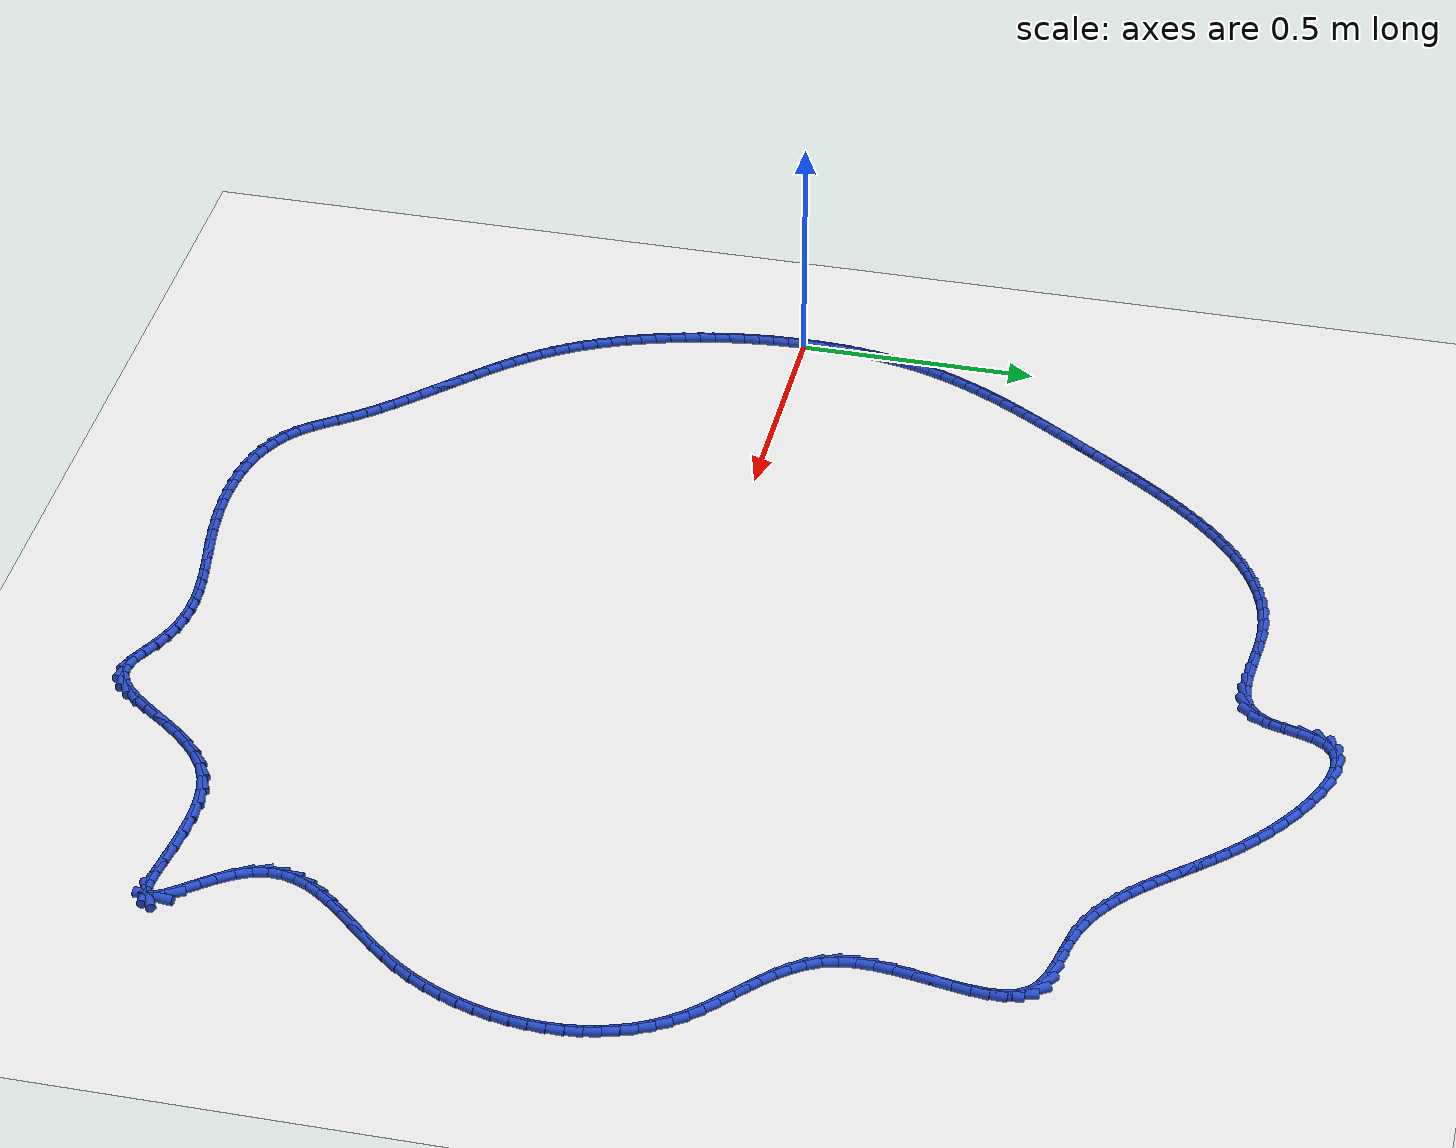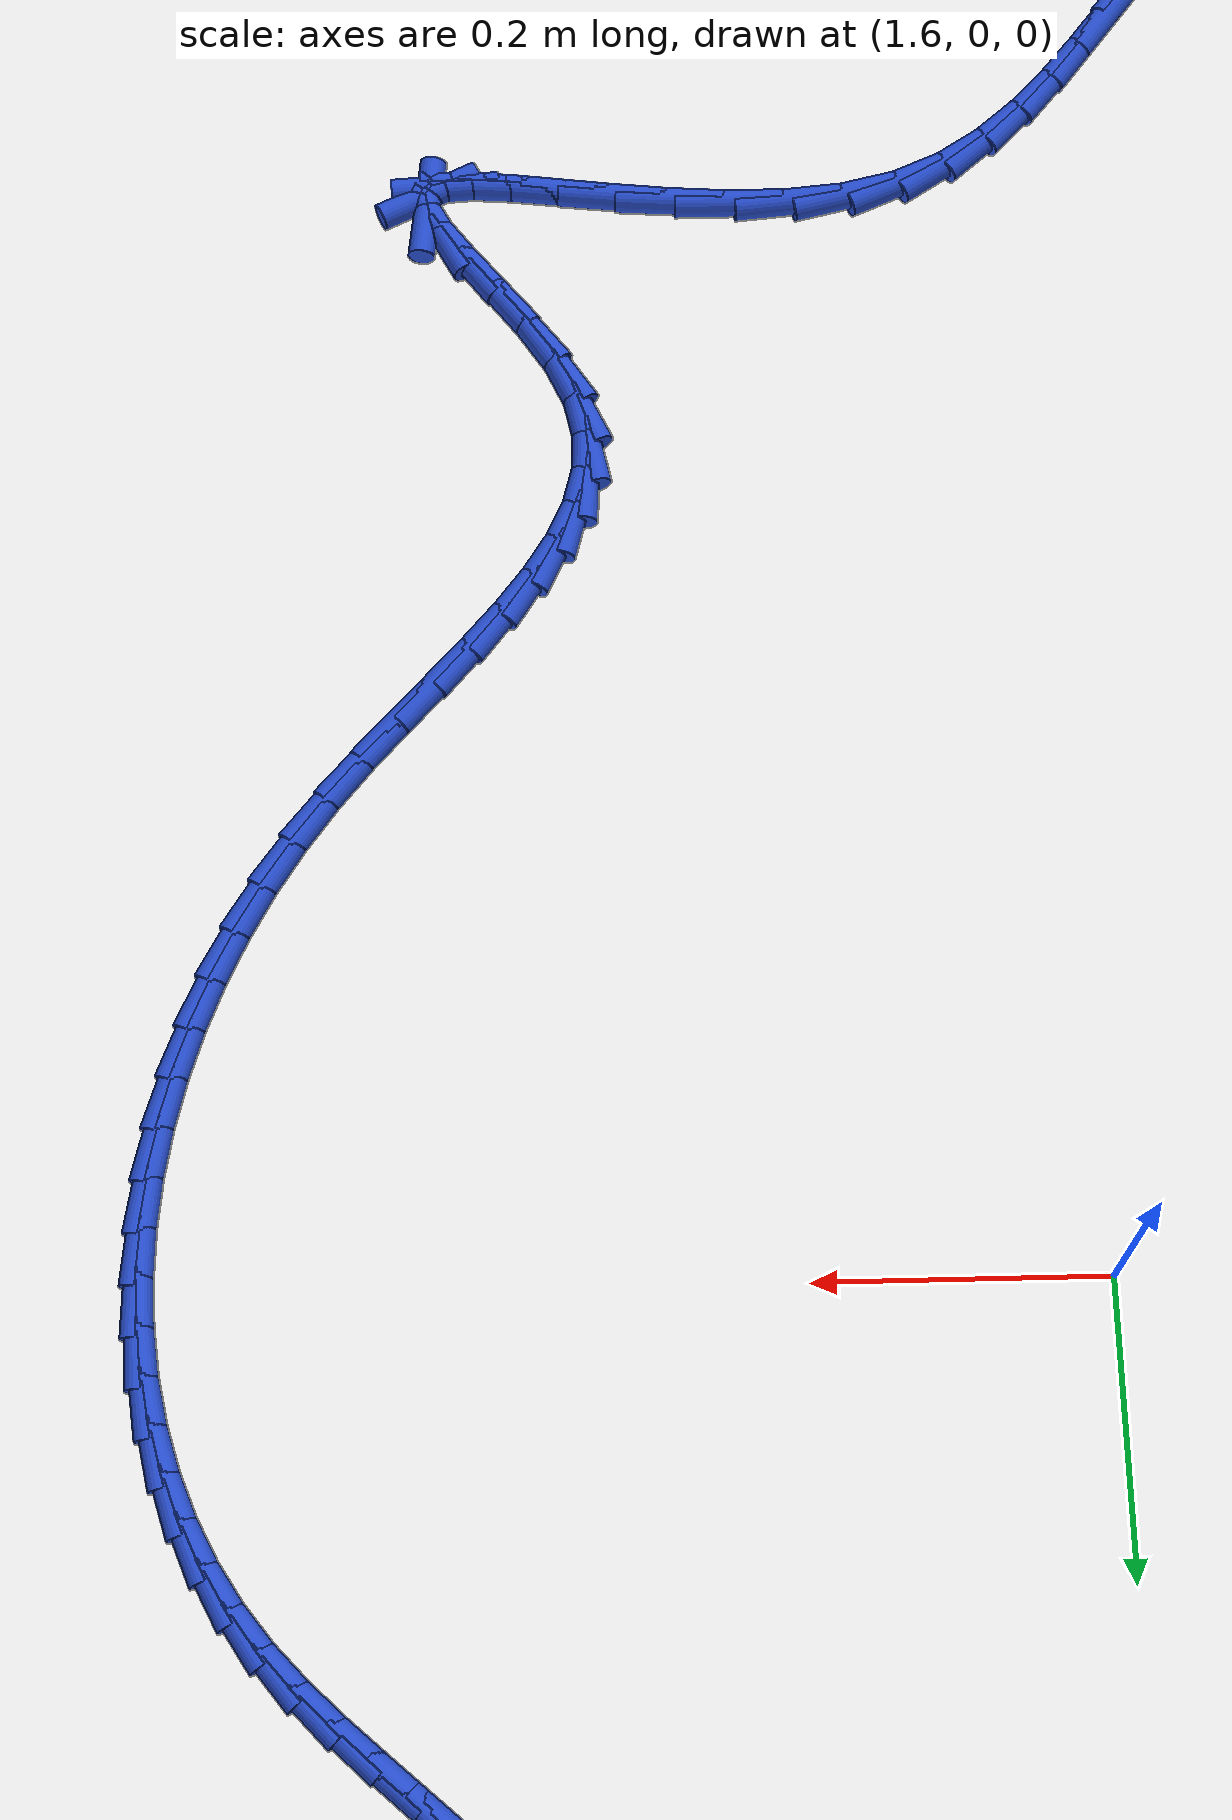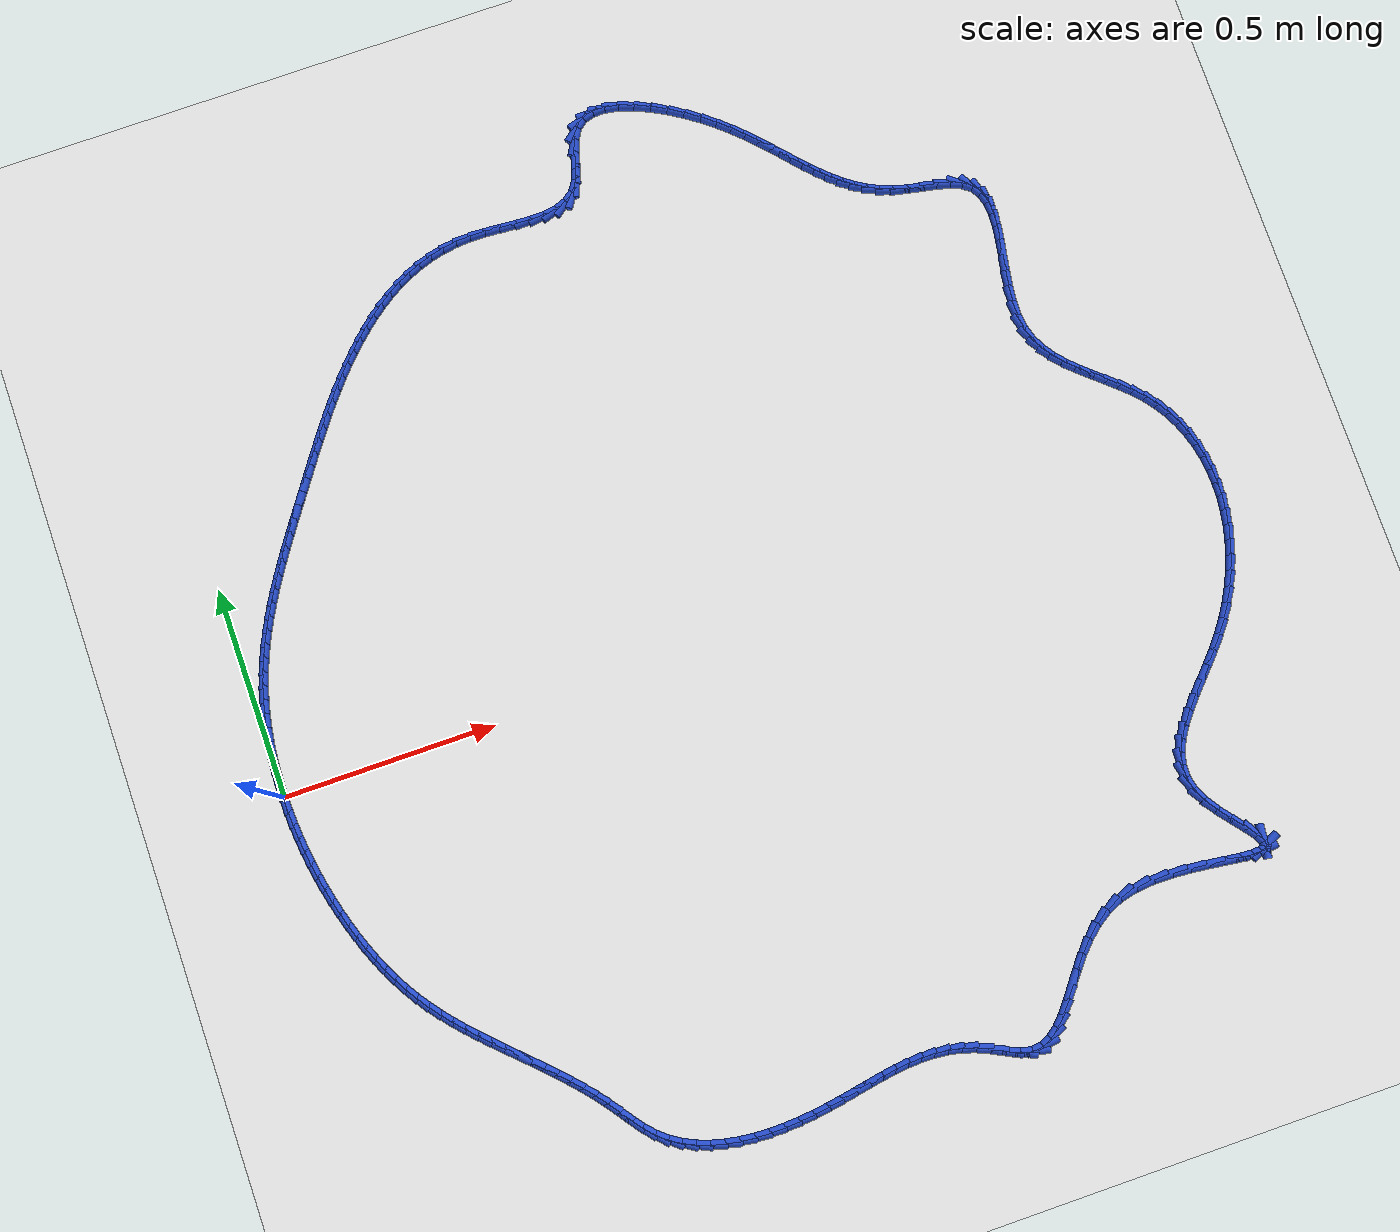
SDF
<sdf version="1.6">
 <world name="default">
  <light name="sun" type="directional">
   <pose>0 0 10 0 -0 0</pose>
   <diffuse>0.8 0.8 0.8 1</diffuse>
   <specular>0.2 0.2 0.2 1</specular>
   <attenuation>
    <range>1000</range>
    <constant>0.9</constant>
    <linear>0.01</linear>
    <quadratic>0.001</quadratic>
   </attenuation>
   <direction>-0.5 0.1 -0.9</direction>
  </light>
  <model name="ground_plane">
   <static>1</static>
   <link name="link">
    <collision name="collision">
     <geometry><plane><normal>0 0 1</normal><size>100 100</size></plane></geometry>
     <surface><friction><ode><mu>100</mu><mu2>50</mu2></ode></friction></surface>
    </collision>
    <visual name="visual">
     <cast_shadows>0</cast_shadows>
     <geometry><plane><normal>0 0 1</normal><size>100 100</size></plane></geometry>
     <material>
      <script><uri>file://media/materials/scripts/gazebo.material</uri><name>Gazebo/WhiteGlow</name></script>
     </material>
    </visual>
   </link>
  </model>
  <gravity>0 0 -9.8</gravity>
  <magnetic_field>6e-06 2.3e-05 -4.2e-05</magnetic_field>
  <atmosphere type="adiabatic"/>
  <physics name="default_physics" default="0" type="ode">
   <max_step_size>0.001</max_step_size>
   <real_time_factor>1</real_time_factor>
   <real_time_update_rate>1000</real_time_update_rate>
  </physics>
  <scene><ambient>0.4 0.4 0.4 1</ambient><background>0.7 0.7 0.7 1</background><shadows>1</shadows></scene>
  <spherical_coordinates>
   <surface_model>EARTH_WGS84</surface_model>
   <latitude_deg>0</latitude_deg>
   <longitude_deg>0</longitude_deg>
   <elevation>0</elevation>
   <heading_deg>0</heading_deg>
  </spherical_coordinates>
  <model name="line">
   <link name="link_0">
    <pose>2.168404344971009e-18 8.326672684688674e-17 0.01 0 1.57 1.5648901160144602</pose>
    <collision name="collision">
     <geometry><cylinder><radius>0.01</radius><length>0.08</length></cylinder></geometry>
    </collision>
    <visual name="visual">
     <material>
      <script><name>Gazebo/Blue</name><uri>file://media/materials/scripts/gazebo.material</uri></script>
     </material>
     <geometry><cylinder><radius>0.01</radius><length>0.08</length></cylinder></geometry>
    </visual>
   </link>
   <link name="link_1">
    <pose>0.00019060022542057974 0.032270776686496104 0.01 0 1.57 1.53334410636547</pose>
    <collision name="collision">
     <geometry><cylinder><radius>0.01</radius><length>0.08</length></cylinder></geometry>
    </collision>
    <visual name="visual">
     <material>
      <script><name>Gazebo/Blue</name><uri>file://media/materials/scripts/gazebo.material</uri></script>
     </material>
     <geometry><cylinder><radius>0.01</radius><length>0.08</length></cylinder></geometry>
    </visual>
   </link>
   <link name="link_2">
    <pose>0.0014006621932245817 0.064565154134899 0.01 0 1.57 1.5004089411498507</pose>
    <collision name="collision">
     <geometry><cylinder><radius>0.01</radius><length>0.08</length></cylinder></geometry>
    </collision>
    <visual name="visual">
     <material>
      <script><name>Gazebo/Blue</name><uri>file://media/materials/scripts/gazebo.material</uri></script>
     </material>
     <geometry><cylinder><radius>0.01</radius><length>0.08</length></cylinder></geometry>
    </visual>
   </link>
   <link name="link_3">
    <pose>0.003674035857047578 0.09680982430764065 0.01 0 1.57 1.4659406801537984</pose>
    <collision name="collision">
     <geometry><cylinder><radius>0.01</radius><length>0.08</length></cylinder></geometry>
    </collision>
    <visual name="visual">
     <material>
      <script><name>Gazebo/Blue</name><uri>file://media/materials/scripts/gazebo.material</uri></script>
     </material>
     <geometry><cylinder><radius>0.01</radius><length>0.08</length></cylinder></geometry>
    </visual>
   </link>
   <link name="link_4">
    <pose>0.007054571170525126 0.12893147916715292 0.01 0 1.57 1.4297961804503372</pose>
    <collision name="collision">
     <geometry><cylinder><radius>0.01</radius><length>0.08</length></cylinder></geometry>
    </collision>
    <visual name="visual">
     <material>
      <script><name>Gazebo/Blue</name><uri>file://media/materials/scripts/gazebo.material</uri></script>
     </material>
     <geometry><cylinder><radius>0.01</radius><length>0.08</length></cylinder></geometry>
    </visual>
   </link>
   <link name="link_5">
    <pose>0.011586118087292804 0.16085681067586768 0.01 0 1.57 1.3918350641744912</pose>
    <collision name="collision">
     <geometry><cylinder><radius>0.01</radius><length>0.08</length></cylinder></geometry>
    </collision>
    <visual name="visual">
     <material>
      <script><name>Gazebo/Blue</name><uri>file://media/materials/scripts/gazebo.material</uri></script>
     </material>
     <geometry><cylinder><radius>0.01</radius><length>0.08</length></cylinder></geometry>
    </visual>
   </link>
   <link name="link_6">
    <pose>0.01731252656098618 0.1925125107962168 0.01 0 1.57 1.351922615156664</pose>
    <collision name="collision">
     <geometry><cylinder><radius>0.01</radius><length>0.08</length></cylinder></geometry>
    </collision>
    <visual name="visual">
     <material>
      <script><name>Gazebo/Blue</name><uri>file://media/materials/scripts/gazebo.material</uri></script>
     </material>
     <geometry><cylinder><radius>0.01</radius><length>0.08</length></cylinder></geometry>
    </visual>
   </link>
   <link name="link_7">
    <pose>0.02427764654524081 0.2238252714906321 0.01 0 1.57 1.3099337440673813</pose>
    <collision name="collision">
     <geometry><cylinder><radius>0.01</radius><length>0.08</length></cylinder></geometry>
    </collision>
    <visual name="visual">
     <material>
      <script><name>Gazebo/Blue</name><uri>file://media/materials/scripts/gazebo.material</uri></script>
     </material>
     <geometry><cylinder><radius>0.01</radius><length>0.08</length></cylinder></geometry>
    </visual>
   </link>
   <link name="link_8">
    <pose>0.032525327993692274 0.25472178472154544 0.01 0 1.57 1.2658759121494043</pose>
    <collision name="collision">
     <geometry><cylinder><radius>0.01</radius><length>0.08</length></cylinder></geometry>
    </collision>
    <visual name="visual">
     <material>
      <script><name>Gazebo/Blue</name><uri>file://media/materials/scripts/gazebo.material</uri></script>
     </material>
     <geometry><cylinder><radius>0.01</radius><length>0.08</length></cylinder></geometry>
    </visual>
   </link>
   <link name="link_9">
    <pose>0.04209624716913201 0.2851311646936632 0.01 0 1.57 1.2223420193794066</pose>
    <collision name="collision">
     <geometry><cylinder><radius>0.01</radius><length>0.08</length></cylinder></geometry>
    </collision>
    <visual name="visual">
     <material>
      <script><name>Gazebo/Blue</name><uri>file://media/materials/scripts/gazebo.material</uri></script>
     </material>
     <geometry><cylinder><radius>0.01</radius><length>0.08</length></cylinder></geometry>
    </visual>
   </link>
   <link name="link_10">
    <pose>0.052960229221948235 0.31503660099838793 0.01 0 1.57 1.1820578470017629</pose>
    <collision name="collision">
     <geometry><cylinder><radius>0.01</radius><length>0.08</length></cylinder></geometry>
    </collision>
    <visual name="visual">
     <material>
      <script><name>Gazebo/Blue</name><uri>file://media/materials/scripts/gazebo.material</uri></script>
     </material>
     <geometry><cylinder><radius>0.01</radius><length>0.08</length></cylinder></geometry>
    </visual>
   </link>
   <link name="link_11">
    <pose>0.0650174191005162 0.3444744649449694 0.01 0 1.57 1.1452625385008472</pose>
    <collision name="collision">
     <geometry><cylinder><radius>0.01</radius><length>0.08</length></cylinder></geometry>
    </collision>
    <visual name="visual">
     <material>
      <script><name>Gazebo/Blue</name><uri>file://media/materials/scripts/gazebo.material</uri></script>
     </material>
     <geometry><cylinder><radius>0.01</radius><length>0.08</length></cylinder></geometry>
    </visual>
   </link>
   <link name="link_12">
    <pose>0.07816502226483196 0.37348337133560167 0.01 0 1.57 1.1120261956993076</pose>
    <collision name="collision">
     <geometry><cylinder><radius>0.01</radius><length>0.08</length></cylinder></geometry>
    </collision>
    <visual name="visual">
     <material>
      <script><name>Gazebo/Blue</name><uri>file://media/materials/scripts/gazebo.material</uri></script>
     </material>
     <geometry><cylinder><radius>0.01</radius><length>0.08</length></cylinder></geometry>
    </visual>
   </link>
   <link name="link_13">
    <pose>0.09230024417489151 0.4021019349724785 0.01 0 1.57 1.082371617127295</pose>
    <collision name="collision">
     <geometry><cylinder><radius>0.01</radius><length>0.08</length></cylinder></geometry>
    </collision>
    <visual name="visual">
     <material>
      <script><name>Gazebo/Blue</name><uri>file://media/materials/scripts/gazebo.material</uri></script>
     </material>
     <geometry><cylinder><radius>0.01</radius><length>0.08</length></cylinder></geometry>
    </visual>
   </link>
   <link name="link_14">
    <pose>0.107320290290691 0.43036877065779433 0.01 0 1.57 1.0562868428455916</pose>
    <collision name="collision">
     <geometry><cylinder><radius>0.01</radius><length>0.08</length></cylinder></geometry>
    </collision>
    <visual name="visual">
     <material>
      <script><name>Gazebo/Blue</name><uri>file://media/materials/scripts/gazebo.material</uri></script>
     </material>
     <geometry><cylinder><radius>0.01</radius><length>0.08</length></cylinder></geometry>
    </visual>
   </link>
   <link name="link_15">
    <pose>0.1231223660722264 0.45832249319374324 0.01 0 1.57 1.0337366831834836</pose>
    <collision name="collision">
     <geometry><cylinder><radius>0.01</radius><length>0.08</length></cylinder></geometry>
    </collision>
    <visual name="visual">
     <material>
      <script><name>Gazebo/Blue</name><uri>file://media/materials/scripts/gazebo.material</uri></script>
     </material>
     <geometry><cylinder><radius>0.01</radius><length>0.08</length></cylinder></geometry>
    </visual>
   </link>
   <link name="link_16">
    <pose>0.13960367697949386 0.48600171738251907 0.01 0 1.57 1.0146727394297614</pose>
    <collision name="collision">
     <geometry><cylinder><radius>0.01</radius><length>0.08</length></cylinder></geometry>
    </collision>
    <visual name="visual">
     <material>
      <script><name>Gazebo/Blue</name><uri>file://media/materials/scripts/gazebo.material</uri></script>
     </material>
     <geometry><cylinder><radius>0.01</radius><length>0.08</length></cylinder></geometry>
    </visual>
   </link>
   <link name="link_17">
    <pose>0.1566614284724893 0.5134450580263159 0.01 0 1.57 0.9990417347318468</pose>
    <collision name="collision">
     <geometry><cylinder><radius>0.01</radius><length>0.08</length></cylinder></geometry>
    </collision>
    <visual name="visual">
     <material>
      <script><name>Gazebo/Blue</name><uri>file://media/materials/scripts/gazebo.material</uri></script>
     </material>
     <geometry><cylinder><radius>0.01</radius><length>0.08</length></cylinder></geometry>
    </visual>
   </link>
   <link name="link_18">
    <pose>0.17419282601120892 0.540691129927328 0.01 0 1.57 0.9867921795562007</pose>
    <collision name="collision">
     <geometry><cylinder><radius>0.01</radius><length>0.08</length></cylinder></geometry>
    </collision>
    <visual name="visual">
     <material>
      <script><name>Gazebo/Blue</name><uri>file://media/materials/scripts/gazebo.material</uri></script>
     </material>
     <geometry><cylinder><radius>0.01</radius><length>0.08</length></cylinder></geometry>
    </visual>
   </link>
   <link name="link_19">
    <pose>0.19209507505564863 0.5677785478877495 0.01 0 1.57 0.9778795110179378</pose>
    <collision name="collision">
     <geometry><cylinder><radius>0.01</radius><length>0.08</length></cylinder></geometry>
    </collision>
    <visual name="visual">
     <material>
      <script><name>Gazebo/Blue</name><uri>file://media/materials/scripts/gazebo.material</uri></script>
     </material>
     <geometry><cylinder><radius>0.01</radius><length>0.08</length></cylinder></geometry>
    </visual>
   </link>
   <link name="link_20">
    <pose>0.2102653810658046 0.5947459267097743 0.01 0 1.57 0.9722698907152042</pose>
    <collision name="collision">
     <geometry><cylinder><radius>0.01</radius><length>0.08</length></cylinder></geometry>
    </collision>
    <visual name="visual">
     <material>
      <script><name>Gazebo/Blue</name><uri>file://media/materials/scripts/gazebo.material</uri></script>
     </material>
     <geometry><cylinder><radius>0.01</radius><length>0.08</length></cylinder></geometry>
    </visual>
   </link>
   <link name="link_21">
    <pose>0.22860094950167287 0.6216318811955966 0.01 0 1.57 0.9699428429115506</pose>
    <collision name="collision">
     <geometry><cylinder><radius>0.01</radius><length>0.08</length></cylinder></geometry>
    </collision>
    <visual name="visual">
     <material>
      <script><name>Gazebo/Blue</name><uri>file://media/materials/scripts/gazebo.material</uri></script>
     </material>
     <geometry><cylinder><radius>0.01</radius><length>0.08</length></cylinder></geometry>
    </visual>
   </link>
   <link name="link_22">
    <pose>0.24699898582324953 0.6484750261474106 0.01 0 1.57 0.9704906754867219</pose>
    <collision name="collision">
     <geometry><cylinder><radius>0.01</radius><length>0.08</length></cylinder></geometry>
    </collision>
    <visual name="visual">
     <material>
      <script><name>Gazebo/Blue</name><uri>file://media/materials/scripts/gazebo.material</uri></script>
     </material>
     <geometry><cylinder><radius>0.01</radius><length>0.08</length></cylinder></geometry>
    </visual>
   </link>
   <link name="link_23">
    <pose>0.26536793924448093 0.6753072486074341 0.01 0 1.57 0.9700519413748757</pose>
    <collision name="collision">
     <geometry><cylinder><radius>0.01</radius><length>0.08</length></cylinder></geometry>
    </collision>
    <visual name="visual">
     <material>
      <script><name>Gazebo/Blue</name><uri>file://media/materials/scripts/gazebo.material</uri></script>
     </material>
     <geometry><cylinder><radius>0.01</radius><length>0.08</length></cylinder></geometry>
    </visual>
   </link>
   <link name="link_24">
    <pose>0.28372426789440097 0.702095807909101 0.01 0 1.57 0.9664612072575871</pose>
    <collision name="collision">
     <geometry><cylinder><radius>0.01</radius><length>0.08</length></cylinder></geometry>
    </collision>
    <visual name="visual">
     <material>
      <script><name>Gazebo/Blue</name><uri>file://media/materials/scripts/gazebo.material</uri></script>
     </material>
     <geometry><cylinder><radius>0.01</radius><length>0.08</length></cylinder></geometry>
    </visual>
   </link>
   <link name="link_25">
    <pose>0.302144658419343 0.7287719253321949 0.01 0 1.57 0.9596743345228159</pose>
    <collision name="collision">
     <geometry><cylinder><radius>0.01</radius><length>0.08</length></cylinder></geometry>
    </collision>
    <visual name="visual">
     <material>
      <script><name>Gazebo/Blue</name><uri>file://media/materials/scripts/gazebo.material</uri></script>
     </material>
     <geometry><cylinder><radius>0.01</radius><length>0.08</length></cylinder></geometry>
    </visual>
   </link>
   <link name="link_26">
    <pose>0.320706450802204 0.7552664312290914 0.01 0 1.57 0.9496638863237736</pose>
    <collision name="collision">
     <geometry><cylinder><radius>0.01</radius><length>0.08</length></cylinder></geometry>
    </collision>
    <visual name="visual">
     <material>
      <script><name>Gazebo/Blue</name><uri>file://media/materials/scripts/gazebo.material</uri></script>
     </material>
     <geometry><cylinder><radius>0.01</radius><length>0.08</length></cylinder></geometry>
    </visual>
   </link>
   <link name="link_27">
    <pose>0.3394869850258814 0.7815101559521671 0.01 0 1.57 0.936397704067074</pose>
    <collision name="collision">
     <geometry><cylinder><radius>0.01</radius><length>0.08</length></cylinder></geometry>
    </collision>
    <visual name="visual">
     <material>
      <script><name>Gazebo/Blue</name><uri>file://media/materials/scripts/gazebo.material</uri></script>
     </material>
     <geometry><cylinder><radius>0.01</radius><length>0.08</length></cylinder></geometry>
    </visual>
   </link>
   <link name="link_28">
    <pose>0.3585636010732723 0.8074339298537975 0.01 0 1.57 0.9198419283635109</pose>
    <collision name="collision">
     <geometry><cylinder><radius>0.01</radius><length>0.08</length></cylinder></geometry>
    </collision>
    <visual name="visual">
     <material>
      <script><name>Gazebo/Blue</name><uri>file://media/materials/scripts/gazebo.material</uri></script>
     </material>
     <geometry><cylinder><radius>0.01</radius><length>0.08</length></cylinder></geometry>
    </visual>
   </link>
   <link name="link_29">
    <pose>0.3780136389272735 0.8329685832863584 0.01 0 1.57 0.89996518725371</pose>
    <collision name="collision">
     <geometry><cylinder><radius>0.01</radius><length>0.08</length></cylinder></geometry>
    </collision>
    <visual name="visual">
     <material>
      <script><name>Gazebo/Blue</name><uri>file://media/materials/scripts/gazebo.material</uri></script>
     </material>
     <geometry><cylinder><radius>0.01</radius><length>0.08</length></cylinder></geometry>
    </visual>
   </link>
   <link name="link_30">
    <pose>0.39791443857078285 0.8580449466022263 0.01 0 1.57 0.8767440298176872</pose>
    <collision name="collision">
     <geometry><cylinder><radius>0.01</radius><length>0.08</length></cylinder></geometry>
    </collision>
    <visual name="visual">
     <material>
      <script><name>Gazebo/Blue</name><uri>file://media/materials/scripts/gazebo.material</uri></script>
     </material>
     <geometry><cylinder><radius>0.01</radius><length>0.08</length></cylinder></geometry>
    </visual>
   </link>
   <link name="link_31">
    <pose>0.41834333998669704 0.8825938501537769 0.01 0 1.57 0.8501696316024283</pose>
    <collision name="collision">
     <geometry><cylinder><radius>0.01</radius><length>0.08</length></cylinder></geometry>
    </collision>
    <visual name="visual">
     <material>
      <script><name>Gazebo/Blue</name><uri>file://media/materials/scripts/gazebo.material</uri></script>
     </material>
     <geometry><cylinder><radius>0.01</radius><length>0.08</length></cylinder></geometry>
    </visual>
   </link>
   <link name="link_32">
    <pose>0.43937768315791337 0.9065461242933861 0.01 0 1.57 0.8202556971892131</pose>
    <collision name="collision">
     <geometry><cylinder><radius>0.01</radius><length>0.08</length></cylinder></geometry>
    </collision>
    <visual name="visual">
     <material>
      <script><name>Gazebo/Blue</name><uri>file://media/materials/scripts/gazebo.material</uri></script>
     </material>
     <geometry><cylinder><radius>0.01</radius><length>0.08</length></cylinder></geometry>
    </visual>
   </link>
   <link name="link_33">
    <pose>0.46109480806732905 0.9298325993734299 0.01 0 1.57 0.78704732465702</pose>
    <collision name="collision">
     <geometry><cylinder><radius>0.01</radius><length>0.08</length></cylinder></geometry>
    </collision>
    <visual name="visual">
     <material>
      <script><name>Gazebo/Blue</name><uri>file://media/materials/scripts/gazebo.material</uri></script>
     </material>
     <geometry><cylinder><radius>0.01</radius><length>0.08</length></cylinder></geometry>
    </visual>
   </link>
   <link name="link_34">
    <pose>0.48357205469784126 0.9523841057462843 0.01 0 1.57 0.7505631391946278</pose>
    <collision name="collision">
     <geometry><cylinder><radius>0.01</radius><length>0.08</length></cylinder></geometry>
    </collision>
    <visual name="visual">
     <material>
      <script><name>Gazebo/Blue</name><uri>file://media/materials/scripts/gazebo.material</uri></script>
     </material>
     <geometry><cylinder><radius>0.01</radius><length>0.08</length></cylinder></geometry>
    </visual>
   </link>
   <link name="link_35">
    <pose>0.5068865001008068 0.9741282972345386 0.01 0 1.57 0.7093793388604239</pose>
    <collision name="collision">
     <geometry><cylinder><radius>0.01</radius><length>0.08</length></cylinder></geometry>
    </collision>
    <visual name="visual">
     <material>
      <script><name>Gazebo/Blue</name><uri>file://media/materials/scripts/gazebo.material</uri></script>
     </material>
     <geometry><cylinder><radius>0.01</radius><length>0.08</length></cylinder></geometry>
    </visual>
   </link>
   <link name="link_36">
    <pose>0.5311093953350178 0.9949224426514051 0.01 0 1.57 0.661904533931735</pose>
    <collision name="collision">
     <geometry><cylinder><radius>0.01</radius><length>0.08</length></cylinder></geometry>
    </collision>
    <visual name="visual">
     <material>
      <script><name>Gazebo/Blue</name><uri>file://media/materials/scripts/gazebo.material</uri></script>
     </material>
     <geometry><cylinder><radius>0.01</radius><length>0.08</length></cylinder></geometry>
    </visual>
   </link>
   <link name="link_37">
    <pose>0.5563062858925848 1.014554880690486 0.01 0 1.57 0.607928343341535</pose>
    <collision name="collision">
     <geometry><cylinder><radius>0.01</radius><length>0.08</length></cylinder></geometry>
    </collision>
    <visual name="visual">
     <material>
      <script><name>Gazebo/Blue</name><uri>file://media/materials/scripts/gazebo.material</uri></script>
     </material>
     <geometry><cylinder><radius>0.01</radius><length>0.08</length></cylinder></geometry>
    </visual>
   </link>
   <link name="link_38">
    <pose>0.5825424784225489 1.0328110645333466 0.01 0 1.57 0.5474065831876195</pose>
    <collision name="collision">
     <geometry><cylinder><radius>0.01</radius><length>0.08</length></cylinder></geometry>
    </collision>
    <visual name="visual">
     <material>
      <script><name>Gazebo/Blue</name><uri>file://media/materials/scripts/gazebo.material</uri></script>
     </material>
     <geometry><cylinder><radius>0.01</radius><length>0.08</length></cylinder></geometry>
    </visual>
   </link>
   <link name="link_39">
    <pose>0.6098832795739517 1.049476447361553 0.01 0 1.57 0.4804702966707305</pose>
    <collision name="collision">
     <geometry><cylinder><radius>0.01</radius><length>0.08</length></cylinder></geometry>
    </collision>
    <visual name="visual">
     <material>
      <script><name>Gazebo/Blue</name><uri>file://media/materials/scripts/gazebo.material</uri></script>
     </material>
     <geometry><cylinder><radius>0.01</radius><length>0.08</length></cylinder></geometry>
    </visual>
   </link>
   <link name="link_40">
    <pose>0.6383939959958345 1.0643364823566703 0.01 0 1.57 0.40749841973965417</pose>
    <collision name="collision">
     <geometry><cylinder><radius>0.01</radius><length>0.08</length></cylinder></geometry>
    </collision>
    <visual name="visual">
     <material>
      <script><name>Gazebo/Blue</name><uri>file://media/materials/scripts/gazebo.material</uri></script>
     </material>
     <geometry><cylinder><radius>0.01</radius><length>0.08</length></cylinder></geometry>
    </visual>
   </link>
   <link name="link_41">
    <pose>0.6681399343372383 1.0771766227002644 0.01 0 1.57 0.32917852488138627</pose>
    <collision name="collision">
     <geometry><cylinder><radius>0.01</radius><length>0.08</length></cylinder></geometry>
    </collision>
    <visual name="visual">
     <material>
      <script><name>Gazebo/Blue</name><uri>file://media/materials/scripts/gazebo.material</uri></script>
     </material>
     <geometry><cylinder><radius>0.01</radius><length>0.08</length></cylinder></geometry>
    </visual>
   </link>
   <link name="link_42">
    <pose>0.699186401247205 1.087782321573901 0.01 0 1.57 0.24653549059472318</pose>
    <collision name="collision">
     <geometry><cylinder><radius>0.01</radius><length>0.08</length></cylinder></geometry>
    </collision>
    <visual name="visual">
     <material>
      <script><name>Gazebo/Blue</name><uri>file://media/materials/scripts/gazebo.material</uri></script>
     </material>
     <geometry><cylinder><radius>0.01</radius><length>0.08</length></cylinder></geometry>
    </visual>
   </link>
   <link name="link_43">
    <pose>0.7315987033747753 1.095939032159146 0.01 0 1.57 0.16090811380330003</pose>
    <collision name="collision">
     <geometry><cylinder><radius>0.01</radius><length>0.08</length></cylinder></geometry>
    </collision>
    <visual name="visual">
     <material>
      <script><name>Gazebo/Blue</name><uri>file://media/materials/scripts/gazebo.material</uri></script>
     </material>
     <geometry><cylinder><radius>0.01</radius><length>0.08</length></cylinder></geometry>
    </visual>
   </link>
   <link name="link_44">
    <pose>0.7654421473689907 1.1014322076375642 0.01 0 1.57 0.07386372127714673</pose>
    <collision name="collision">
     <geometry><cylinder><radius>0.01</radius><length>0.08</length></cylinder></geometry>
    </collision>
    <visual name="visual">
     <material>
      <script><name>Gazebo/Blue</name><uri>file://media/materials/scripts/gazebo.material</uri></script>
     </material>
     <geometry><cylinder><radius>0.01</radius><length>0.08</length></cylinder></geometry>
    </visual>
   </link>
   <link name="link_45">
    <pose>0.8007820398788928 1.1040473011907221 0.01 0 1.57 -0.008468546841838393</pose>
    <collision name="collision">
     <geometry><cylinder><radius>0.01</radius><length>0.08</length></cylinder></geometry>
    </collision>
    <visual name="visual">
     <material>
      <script><name>Gazebo/Blue</name><uri>file://media/materials/scripts/gazebo.material</uri></script>
     </material>
     <geometry><cylinder><radius>0.01</radius><length>0.08</length></cylinder></geometry>
    </visual>
   </link>
   <link name="link_46">
    <pose>0.8375799641351765 1.1037356687957338 0.01 0 1.57 -0.05910049594051212</pose>
    <collision name="collision">
     <geometry><cylinder><radius>0.01</radius><length>0.08</length></cylinder></geometry>
    </collision>
    <visual name="visual">
     <material>
      <script><name>Gazebo/Blue</name><uri>file://media/materials/scripts/gazebo.material</uri></script>
     </material>
     <geometry><cylinder><radius>0.01</radius><length>0.08</length></cylinder></geometry>
    </visual>
   </link>
   <link name="link_47">
    <pose>0.8751315999142886 1.1015137609511574 0.01 0 1.57 -0.07204867757715043</pose>
    <collision name="collision">
     <geometry><cylinder><radius>0.01</radius><length>0.08</length></cylinder></geometry>
    </collision>
    <visual name="visual">
     <material>
      <script><name>Gazebo/Blue</name><uri>file://media/materials/scripts/gazebo.material</uri></script>
     </material>
     <geometry><cylinder><radius>0.01</radius><length>0.08</length></cylinder></geometry>
    </visual>
   </link>
   <link name="link_48">
    <pose>0.9124694623953131 1.0988189527942498 0.01 0 1.57 -0.04779239952121264</pose>
    <collision name="collision">
     <geometry><cylinder><radius>0.01</radius><length>0.08</length></cylinder></geometry>
    </collision>
    <visual name="visual">
     <material>
      <script><name>Gazebo/Blue</name><uri>file://media/materials/scripts/gazebo.material</uri></script>
     </material>
     <geometry><cylinder><radius>0.01</radius><length>0.08</length></cylinder></geometry>
    </visual>
   </link>
   <link name="link_49">
    <pose>0.9486254186768805 1.0970896560493837 0.01 0 1.57 0.01983589813207836</pose>
    <collision name="collision">
     <geometry><cylinder><radius>0.01</radius><length>0.08</length></cylinder></geometry>
    </collision>
    <visual name="visual">
     <material>
      <script><name>Gazebo/Blue</name><uri>file://media/materials/scripts/gazebo.material</uri></script>
     </material>
     <geometry><cylinder><radius>0.01</radius><length>0.08</length></cylinder></geometry>
    </visual>
   </link>
   <link name="link_50">
    <pose>0.9826313358576215 1.0977642824409317 0.01 0 1.57 0.14520868880037902</pose>
    <collision name="collision">
     <geometry><cylinder><radius>0.01</radius><length>0.08</length></cylinder></geometry>
    </collision>
    <visual name="visual">
     <material>
      <script><name>Gazebo/Blue</name><uri>file://media/materials/scripts/gazebo.material</uri></script>
     </material>
     <geometry><cylinder><radius>0.01</radius><length>0.08</length></cylinder></geometry>
    </visual>
   </link>
   <link name="link_51">
    <pose>1.0135190810361663 1.102281243693267 0.01 0 1.57 0.35047463589331795</pose>
    <collision name="collision">
     <geometry><cylinder><radius>0.01</radius><length>0.08</length></cylinder></geometry>
    </collision>
    <visual name="visual">
     <material>
      <script><name>Gazebo/Blue</name><uri>file://media/materials/scripts/gazebo.material</uri></script>
     </material>
     <geometry><cylinder><radius>0.01</radius><length>0.08</length></cylinder></geometry>
    </visual>
   </link>
   <link name="link_52">
    <pose>1.0403205213111448 1.1120789515307619 0.01 0 1.57 0.6495539541764709</pose>
    <collision name="collision">
     <geometry><cylinder><radius>0.01</radius><length>0.08</length></cylinder></geometry>
    </collision>
    <visual name="visual">
     <material>
      <script><name>Gazebo/Blue</name><uri>file://media/materials/scripts/gazebo.material</uri></script>
     </material>
     <geometry><cylinder><radius>0.01</radius><length>0.08</length></cylinder></geometry>
    </visual>
   </link>
   <link name="link_53">
    <pose>1.0620675237811874 1.1285958176777893 0.01 0 1.57 0.9969786287074212</pose>
    <collision name="collision">
     <geometry><cylinder><radius>0.01</radius><length>0.08</length></cylinder></geometry>
    </collision>
    <visual name="visual">
     <material>
      <script><name>Gazebo/Blue</name><uri>file://media/materials/scripts/gazebo.material</uri></script>
     </material>
     <geometry><cylinder><radius>0.01</radius><length>0.08</length></cylinder></geometry>
    </visual>
   </link>
   <link name="link_54">
    <pose>1.0779082851085657 1.1531031609403624 0.01 0 1.57 1.2256817387763668</pose>
    <collision name="collision">
     <geometry><cylinder><radius>0.01</radius><length>0.08</length></cylinder></geometry>
    </collision>
    <visual name="visual">
     <material>
      <script><name>Gazebo/Blue</name><uri>file://media/materials/scripts/gazebo.material</uri></script>
     </material>
     <geometry><cylinder><radius>0.01</radius><length>0.08</length></cylinder></geometry>
    </visual>
   </link>
   <link name="link_55">
    <pose>1.0890072212160025 1.1839762524669761 0.01 0 1.57 1.2994051536043765</pose>
    <collision name="collision">
     <geometry><cylinder><radius>0.01</radius><length>0.08</length></cylinder></geometry>
    </collision>
    <visual name="visual">
     <material>
      <script><name>Gazebo/Blue</name><uri>file://media/materials/scripts/gazebo.material</uri></script>
     </material>
     <geometry><cylinder><radius>0.01</radius><length>0.08</length></cylinder></geometry>
    </visual>
   </link>
   <link name="link_56">
    <pose>1.0982350865183559 1.2171394208474438 0.01 0 1.57 1.2534245858645</pose>
    <collision name="collision">
     <geometry><cylinder><radius>0.01</radius><length>0.08</length></cylinder></geometry>
    </collision>
    <visual name="visual">
     <material>
      <script><name>Gazebo/Blue</name><uri>file://media/materials/scripts/gazebo.material</uri></script>
     </material>
     <geometry><cylinder><radius>0.01</radius><length>0.08</length></cylinder></geometry>
    </visual>
   </link>
   <link name="link_57">
    <pose>1.1085164473224831 1.2484397005960615 0.01 0 1.57 1.0574062370758766</pose>
    <collision name="collision">
     <geometry><cylinder><radius>0.01</radius><length>0.08</length></cylinder></geometry>
    </collision>
    <visual name="visual">
     <material>
      <script><name>Gazebo/Blue</name><uri>file://media/materials/scripts/gazebo.material</uri></script>
     </material>
     <geometry><cylinder><radius>0.01</radius><length>0.08</length></cylinder></geometry>
    </visual>
   </link>
   <link name="link_58">
    <pose>1.1227737843923586 1.2737268280903375 0.01 0 1.57 0.6829167306893079</pose>
    <collision name="collision">
     <geometry><cylinder><radius>0.01</radius><length>0.08</length></cylinder></geometry>
    </collision>
    <visual name="visual">
     <material>
      <script><name>Gazebo/Blue</name><uri>file://media/materials/scripts/gazebo.material</uri></script>
     </material>
     <geometry><cylinder><radius>0.01</radius><length>0.08</length></cylinder></geometry>
    </visual>
   </link>
   <link name="link_59">
    <pose>1.1429402737580883 1.2901322041058931 0.01 0 1.57 0.30402561338667844</pose>
    <collision name="collision">
     <geometry><cylinder><radius>0.01</radius><length>0.08</length></cylinder></geometry>
    </collision>
    <visual name="visual">
     <material>
      <script><name>Gazebo/Blue</name><uri>file://media/materials/scripts/gazebo.material</uri></script>
     </material>
     <geometry><cylinder><radius>0.01</radius><length>0.08</length></cylinder></geometry>
    </visual>
   </link>
   <link name="link_60">
    <pose>1.1683809665544618 1.2981142874375293 0.01 0 1.57 0.018539822388963713</pose>
    <collision name="collision">
     <geometry><cylinder><radius>0.01</radius><length>0.08</length></cylinder></geometry>
    </collision>
    <visual name="visual">
     <material>
      <script><name>Gazebo/Blue</name><uri>file://media/materials/scripts/gazebo.material</uri></script>
     </material>
     <geometry><cylinder><radius>0.01</radius><length>0.08</length></cylinder></geometry>
    </visual>
   </link>
   <link name="link_61">
    <pose>1.1980496005774814 1.2986644016736248 0.01 0 1.57 -0.17742868964590694</pose>
    <collision name="collision">
     <geometry><cylinder><radius>0.01</radius><length>0.08</length></cylinder></geometry>
    </collision>
    <visual name="visual">
     <material>
      <script><name>Gazebo/Blue</name><uri>file://media/materials/scripts/gazebo.material</uri></script>
     </material>
     <geometry><cylinder><radius>0.01</radius><length>0.08</length></cylinder></geometry>
    </visual>
   </link>
   <link name="link_62">
    <pose>1.2308999136231462 1.2927738704025564 0.01 0 1.57 -0.3134429651024757</pose>
    <collision name="collision">
     <geometry><cylinder><radius>0.01</radius><length>0.08</length></cylinder></geometry>
    </collision>
    <visual name="visual">
     <material>
      <script><name>Gazebo/Blue</name><uri>file://media/materials/scripts/gazebo.material</uri></script>
     </material>
     <geometry><cylinder><radius>0.01</radius><length>0.08</length></cylinder></geometry>
    </visual>
   </link>
   <link name="link_63">
    <pose>1.2658856434874581 1.2814340172127026 0.01 0 1.57 -0.4127614722598683</pose>
    <collision name="collision">
     <geometry><cylinder><radius>0.01</radius><length>0.08</length></cylinder></geometry>
    </collision>
    <visual name="visual">
     <material>
      <script><name>Gazebo/Blue</name><uri>file://media/materials/scripts/gazebo.material</uri></script>
     </material>
     <geometry><cylinder><radius>0.01</radius><length>0.08</length></cylinder></geometry>
    </visual>
   </link>
   <link name="link_64">
    <pose>1.3019605279664164 1.2656361656924413 0.01 0 1.57 -0.4899942273169205</pose>
    <collision name="collision">
     <geometry><cylinder><radius>0.01</radius><length>0.08</length></cylinder></geometry>
    </collision>
    <visual name="visual">
     <material>
      <script><name>Gazebo/Blue</name><uri>file://media/materials/scripts/gazebo.material</uri></script>
     </material>
     <geometry><cylinder><radius>0.01</radius><length>0.08</length></cylinder></geometry>
    </visual>
   </link>
   <link name="link_65">
    <pose>1.3380783048560216 1.2463716394301498 0.01 0 1.57 -0.5543566456657815</pose>
    <collision name="collision">
     <geometry><cylinder><radius>0.01</radius><length>0.08</length></cylinder></geometry>
    </collision>
    <visual name="visual">
     <material>
      <script><name>Gazebo/Blue</name><uri>file://media/materials/scripts/gazebo.material</uri></script>
     </material>
     <geometry><cylinder><radius>0.01</radius><length>0.08</length></cylinder></geometry>
    </visual>
   </link>
   <link name="link_66">
    <pose>1.3731927119522758 1.2246317620142066 0.01 0 1.57 -0.6123130681663237</pose>
    <collision name="collision">
     <geometry><cylinder><radius>0.01</radius><length>0.08</length></cylinder></geometry>
    </collision>
    <visual name="visual">
     <material>
      <script><name>Gazebo/Blue</name><uri>file://media/materials/scripts/gazebo.material</uri></script>
     </material>
     <geometry><cylinder><radius>0.01</radius><length>0.08</length></cylinder></geometry>
    </visual>
   </link>
   <link name="link_67">
    <pose>1.40625941168226 1.2014067895443796 0.01 0 1.57 -0.6675079966193087</pose>
    <collision name="collision">
     <geometry><cylinder><radius>0.01</radius><length>0.08</length></cylinder></geometry>
    </collision>
    <visual name="visual">
     <material>
      <script><name>Gazebo/Blue</name><uri>file://media/materials/scripts/gazebo.material</uri></script>
     </material>
     <geometry><cylinder><radius>0.01</radius><length>0.08</length></cylinder></geometry>
    </visual>
   </link>
   <link name="link_68">
    <pose>1.4366348558494482 1.1774646819627517 0.01 0 1.57 -0.7177215172570065</pose>
    <collision name="collision">
     <geometry><cylinder><radius>0.01</radius><length>0.08</length></cylinder></geometry>
    </collision>
    <visual name="visual">
     <material>
      <script><name>Gazebo/Blue</name><uri>file://media/materials/scripts/gazebo.material</uri></script>
     </material>
     <geometry><cylinder><radius>0.01</radius><length>0.08</length></cylinder></geometry>
    </visual>
   </link>
   <link name="link_69">
    <pose>1.464566184350316 1.1530793827717698 0.01 0 1.57 -0.7609706291626978</pose>
    <collision name="collision">
     <geometry><cylinder><radius>0.01</radius><length>0.08</length></cylinder></geometry>
    </collision>
    <visual name="visual">
     <material>
      <script><name>Gazebo/Blue</name><uri>file://media/materials/scripts/gazebo.material</uri></script>
     </material>
     <geometry><cylinder><radius>0.01</radius><length>0.08</length></cylinder></geometry>
    </visual>
   </link>
   <link name="link_70">
    <pose>1.4904205084487963 1.1284582938547942 0.01 0 1.57 -0.7957483851435907</pose>
    <collision name="collision">
     <geometry><cylinder><radius>0.01</radius><length>0.08</length></cylinder></geometry>
    </collision>
    <visual name="visual">
     <material>
      <script><name>Gazebo/Blue</name><uri>file://media/materials/scripts/gazebo.material</uri></script>
     </material>
     <geometry><cylinder><radius>0.01</radius><length>0.08</length></cylinder></geometry>
    </visual>
   </link>
   <link name="link_71">
    <pose>1.5145649394088203 1.1038088170951867 0.01 0 1.57 -0.8206857956574665</pose>
    <collision name="collision">
     <geometry><cylinder><radius>0.01</radius><length>0.08</length></cylinder></geometry>
    </collision>
    <visual name="visual">
     <material>
      <script><name>Gazebo/Blue</name><uri>file://media/materials/scripts/gazebo.material</uri></script>
     </material>
     <geometry><cylinder><radius>0.01</radius><length>0.08</length></cylinder></geometry>
    </visual>
   </link>
   <link name="link_72">
    <pose>1.5373665884943204 1.0793383543763067 0.01 0 1.57 -0.8345432050714073</pose>
    <collision name="collision">
     <geometry><cylinder><radius>0.01</radius><length>0.08</length></cylinder></geometry>
    </collision>
    <visual name="visual">
     <material>
      <script><name>Gazebo/Blue</name><uri>file://media/materials/scripts/gazebo.material</uri></script>
     </material>
     <geometry><cylinder><radius>0.01</radius><length>0.08</length></cylinder></geometry>
    </visual>
   </link>
   <link name="link_73">
    <pose>1.559192566969228 1.0552543075815153 0.01 0 1.57 -0.8361915963478432</pose>
    <collision name="collision">
     <geometry><cylinder><radius>0.01</radius><length>0.08</length></cylinder></geometry>
    </collision>
    <visual name="visual">
     <material>
      <script><name>Gazebo/Blue</name><uri>file://media/materials/scripts/gazebo.material</uri></script>
     </material>
     <geometry><cylinder><radius>0.01</radius><length>0.08</length></cylinder></geometry>
    </visual>
   </link>
   <link name="link_74">
    <pose>1.5804099860974758 1.0317640785941733 0.01 0 1.57 -0.8246094535677373</pose>
    <collision name="collision">
     <geometry><cylinder><radius>0.01</radius><length>0.08</length></cylinder></geometry>
    </collision>
    <visual name="visual">
     <material>
      <script><name>Gazebo/Blue</name><uri>file://media/materials/scripts/gazebo.material</uri></script>
     </material>
     <geometry><cylinder><radius>0.01</radius><length>0.08</length></cylinder></geometry>
    </visual>
   </link>
   <link name="link_75">
    <pose>1.6013859571429945 1.0090750692976413 0.01 0 1.57 -0.7989252985837583</pose>
    <collision name="collision">
     <geometry><cylinder><radius>0.01</radius><length>0.08</length></cylinder></geometry>
    </collision>
    <visual name="visual">
     <material>
      <script><name>Gazebo/Blue</name><uri>file://media/materials/scripts/gazebo.material</uri></script>
     </material>
     <geometry><cylinder><radius>0.01</radius><length>0.08</length></cylinder></geometry>
    </visual>
   </link>
   <link name="link_76">
    <pose>1.6224875913697177 0.9873946815752804 0.01 0 1.57 -0.7585364049812264</pose>
    <collision name="collision">
     <geometry><cylinder><radius>0.01</radius><length>0.08</length></cylinder></geometry>
    </collision>
    <visual name="visual">
     <material>
      <script><name>Gazebo/Blue</name><uri>file://media/materials/scripts/gazebo.material</uri></script>
     </material>
     <geometry><cylinder><radius>0.01</radius><length>0.08</length></cylinder></geometry>
    </visual>
   </link>
   <link name="link_77">
    <pose>1.6440820000415761 0.9669303173104505 0.01 0 1.57 -0.7033239725984757</pose>
    <collision name="collision">
     <geometry><cylinder><radius>0.01</radius><length>0.08</length></cylinder></geometry>
    </collision>
    <visual name="visual">
     <material>
      <script><name>Gazebo/Blue</name><uri>file://media/materials/scripts/gazebo.material</uri></script>
     </material>
     <geometry><cylinder><radius>0.01</radius><length>0.08</length></cylinder></geometry>
    </visual>
   </link>
   <link name="link_78">
    <pose>1.6665362944225022 0.9478893783865131 0.01 0 1.57 -0.633951383910856</pose>
    <collision name="collision">
     <geometry><cylinder><radius>0.01</radius><length>0.08</length></cylinder></geometry>
    </collision>
    <visual name="visual">
     <material>
      <script><name>Gazebo/Blue</name><uri>file://media/materials/scripts/gazebo.material</uri></script>
     </material>
     <geometry><cylinder><radius>0.01</radius><length>0.08</length></cylinder></geometry>
    </visual>
   </link>
   <link name="link_79">
    <pose>1.6902175857764274 0.9304792666868279 0.01 0 1.57 -0.552165352754267</pose>
    <collision name="collision">
     <geometry><cylinder><radius>0.01</radius><length>0.08</length></cylinder></geometry>
    </collision>
    <visual name="visual">
     <material>
      <script><name>Gazebo/Blue</name><uri>file://media/materials/scripts/gazebo.material</uri></script>
     </material>
     <geometry><cylinder><radius>0.01</radius><length>0.08</length></cylinder></geometry>
    </visual>
   </link>
   <link name="link_80">
    <pose>1.715492985367284 0.9149073840947566 0.01 0 1.57 -0.460940008691091</pose>
    <collision name="collision">
     <geometry><cylinder><radius>0.01</radius><length>0.08</length></cylinder></geometry>
    </collision>
    <visual name="visual">
     <material>
      <script><name>Gazebo/Blue</name><uri>file://media/materials/scripts/gazebo.material</uri></script>
     </material>
     <geometry><cylinder><radius>0.01</radius><length>0.08</length></cylinder></geometry>
    </visual>
   </link>
   <link name="link_81">
    <pose>1.7427296044590042 0.9013811324936591 0.01 0 1.57 -0.36428553761647997</pose>
    <collision name="collision">
     <geometry><cylinder><radius>0.01</radius><length>0.08</length></cylinder></geometry>
    </collision>
    <visual name="visual">
     <material>
      <script><name>Gazebo/Blue</name><uri>file://media/materials/scripts/gazebo.material</uri></script>
     </material>
     <geometry><cylinder><radius>0.01</radius><length>0.08</length></cylinder></geometry>
    </visual>
   </link>
   <link name="link_82">
    <pose>1.7722945543155193 0.8901079137668967 0.01 0 1.57 -0.26734253740722536</pose>
    <collision name="collision">
     <geometry><cylinder><radius>0.01</radius><length>0.08</length></cylinder></geometry>
    </collision>
    <visual name="visual">
     <material>
      <script><name>Gazebo/Blue</name><uri>file://media/materials/scripts/gazebo.material</uri></script>
     </material>
     <geometry><cylinder><radius>0.01</radius><length>0.08</length></cylinder></geometry>
    </visual>
   </link>
   <link name="link_83">
    <pose>1.8045316796122735 0.8812781902708591 0.01 0 1.57 -0.20011474742865712</pose>
    <collision name="collision">
     <geometry><cylinder><radius>0.01</radius><length>0.08</length></cylinder></geometry>
    </collision>
    <visual name="visual">
     <material>
      <script><name>Gazebo/Blue</name><uri>file://media/materials/scripts/gazebo.material</uri></script>
     </material>
     <geometry><cylinder><radius>0.01</radius><length>0.08</length></cylinder></geometry>
    </visual>
   </link>
   <link name="link_84">
    <pose>1.8387593439414476 0.874335810199903 0.01 0 1.57 -0.19201932179187844</pose>
    <collision name="collision">
     <geometry><cylinder><radius>0.01</radius><length>0.08</length></cylinder></geometry>
    </collision>
    <visual name="visual">
     <material>
      <script><name>Gazebo/Blue</name><uri>file://media/materials/scripts/gazebo.material</uri></script>
     </material>
     <geometry><cylinder><radius>0.01</radius><length>0.08</length></cylinder></geometry>
    </visual>
   </link>
   <link name="link_85">
    <pose>1.8728892186223187 0.867700462073753 0.01 0 1.57 -0.2456393977930704</pose>
    <collision name="collision">
     <geometry><cylinder><radius>0.01</radius><length>0.08</length></cylinder></geometry>
    </collision>
    <visual name="visual">
     <material>
      <script><name>Gazebo/Blue</name><uri>file://media/materials/scripts/gazebo.material</uri></script>
     </material>
     <geometry><cylinder><radius>0.01</radius><length>0.08</length></cylinder></geometry>
    </visual>
   </link>
   <link name="link_86">
    <pose>1.9047310703491966 0.8597176414919346 0.01 0 1.57 -0.3817457446013552</pose>
    <collision name="collision">
     <geometry><cylinder><radius>0.01</radius><length>0.08</length></cylinder></geometry>
    </collision>
    <visual name="visual">
     <material>
      <script><name>Gazebo/Blue</name><uri>file://media/materials/scripts/gazebo.material</uri></script>
     </material>
     <geometry><cylinder><radius>0.01</radius><length>0.08</length></cylinder></geometry>
    </visual>
   </link>
   <link name="link_87">
    <pose>1.9320946658163918 0.8487328440539732 0.01 0 1.57 -0.6457010068586142</pose>
    <collision name="collision">
     <geometry><cylinder><radius>0.01</radius><length>0.08</length></cylinder></geometry>
    </collision>
    <visual name="visual">
     <material>
      <script><name>Gazebo/Blue</name><uri>file://media/materials/scripts/gazebo.material</uri></script>
     </material>
     <geometry><cylinder><radius>0.01</radius><length>0.08</length></cylinder></geometry>
    </visual>
   </link>
   <link name="link_88">
    <pose>1.952823001025882 0.8331152244288017 0.01 0 1.57 -1.0034593341175067</pose>
    <collision name="collision">
     <geometry><cylinder><radius>0.01</radius><length>0.08</length></cylinder></geometry>
    </collision>
    <visual name="visual">
     <material>
      <script><name>Gazebo/Blue</name><uri>file://media/materials/scripts/gazebo.material</uri></script>
     </material>
     <geometry><cylinder><radius>0.01</radius><length>0.08</length></cylinder></geometry>
    </visual>
   </link>
   <link name="link_89">
    <pose>1.9661397437749666 0.8122169673912474 0.01 0 1.57 -1.303896228810537</pose>
    <collision name="collision">
     <geometry><cylinder><radius>0.01</radius><length>0.08</length></cylinder></geometry>
    </collision>
    <visual name="visual">
     <material>
      <script><name>Gazebo/Blue</name><uri>file://media/materials/scripts/gazebo.material</uri></script>
     </material>
     <geometry><cylinder><radius>0.01</radius><length>0.08</length></cylinder></geometry>
    </visual>
   </link>
   <link name="link_90">
    <pose>1.9731152874033415 0.7867051153178107 0.01 0 1.57 -1.508437109540967</pose>
    <collision name="collision">
     <geometry><cylinder><radius>0.01</radius><length>0.08</length></cylinder></geometry>
    </collision>
    <visual name="visual">
     <material>
      <script><name>Gazebo/Blue</name><uri>file://media/materials/scripts/gazebo.material</uri></script>
     </material>
     <geometry><cylinder><radius>0.01</radius><length>0.08</length></cylinder></geometry>
    </visual>
   </link>
   <link name="link_91">
    <pose>1.9749489439962193 0.7573384999649808 0.01 0 1.57 1.5059228273670535</pose>
    <collision name="collision">
     <geometry><cylinder><radius>0.01</radius><length>0.08</length></cylinder></geometry>
    </collision>
    <visual name="visual">
     <material>
      <script><name>Gazebo/Blue</name><uri>file://media/materials/scripts/gazebo.material</uri></script>
     </material>
     <geometry><cylinder><radius>0.01</radius><length>0.08</length></cylinder></geometry>
    </visual>
   </link>
   <link name="link_92">
    <pose>1.972840025638814 0.7248759530892452 0.01 0 1.57 1.4322575975261949</pose>
    <collision name="collision">
     <geometry><cylinder><radius>0.01</radius><length>0.08</length></cylinder></geometry>
    </collision>
    <visual name="visual">
     <material>
      <script><name>Gazebo/Blue</name><uri>file://media/materials/scripts/gazebo.material</uri></script>
     </material>
     <geometry><cylinder><radius>0.01</radius><length>0.08</length></cylinder></geometry>
    </visual>
   </link>
   <link name="link_93">
    <pose>1.9679878444163381 0.6900763064470925 0.01 0 1.57 1.3967506832343952</pose>
    <collision name="collision">
     <geometry><cylinder><radius>0.01</radius><length>0.08</length></cylinder></geometry>
    </collision>
    <visual name="visual">
     <material>
      <script><name>Gazebo/Blue</name><uri>file://media/materials/scripts/gazebo.material</uri></script>
     </material>
     <geometry><cylinder><radius>0.01</radius><length>0.08</length></cylinder></geometry>
    </visual>
   </link>
   <link name="link_94">
    <pose>1.9615917124140043 0.6536983917950098 0.01 0 1.57 1.3915253958359084</pose>
    <collision name="collision">
     <geometry><cylinder><radius>0.01</radius><length>0.08</length></cylinder></geometry>
    </collision>
    <visual name="visual">
     <material>
      <script><name>Gazebo/Blue</name><uri>file://media/materials/scripts/gazebo.material</uri></script>
     </material>
     <geometry><cylinder><radius>0.01</radius><length>0.08</length></cylinder></geometry>
    </visual>
   </link>
   <link name="link_95">
    <pose>1.954850941717026 0.6165010408894864 0.01 0 1.57 1.4141090224717117</pose>
    <collision name="collision">
     <geometry><cylinder><radius>0.01</radius><length>0.08</length></cylinder></geometry>
    </collision>
    <visual name="visual">
     <material>
      <script><name>Gazebo/Blue</name><uri>file://media/materials/scripts/gazebo.material</uri></script>
     </material>
     <geometry><cylinder><radius>0.01</radius><length>0.08</length></cylinder></geometry>
    </visual>
   </link>
   <link name="link_96">
    <pose>1.9489648444106158 0.5792430854870093 0.01 0 1.57 1.4663598435661342</pose>
    <collision name="collision">
     <geometry><cylinder><radius>0.01</radius><length>0.08</length></cylinder></geometry>
    </collision>
    <visual name="visual">
     <material>
      <script><name>Gazebo/Blue</name><uri>file://media/materials/scripts/gazebo.material</uri></script>
     </material>
     <geometry><cylinder><radius>0.01</radius><length>0.08</length></cylinder></geometry>
    </visual>
   </link>
   <link name="link_97">
    <pose>1.9451327325799874 0.5426833573440678 0.01 0 1.57 1.554308639845436</pose>
    <collision name="collision">
     <geometry><cylinder><radius>0.01</radius><length>0.08</length></cylinder></geometry>
    </collision>
    <visual name="visual">
     <material>
      <script><name>Gazebo/Blue</name><uri>file://media/materials/scripts/gazebo.material</uri></script>
     </material>
     <geometry><cylinder><radius>0.01</radius><length>0.08</length></cylinder></geometry>
    </visual>
   </link>
   <link name="link_98">
    <pose>1.9445539183103542 0.5075806882171493 0.01 0 1.57 -1.453545275140963</pose>
    <collision name="collision">
     <geometry><cylinder><radius>0.01</radius><length>0.08</length></cylinder></geometry>
    </collision>
    <visual name="visual">
     <material>
      <script><name>Gazebo/Blue</name><uri>file://media/materials/scripts/gazebo.material</uri></script>
     </material>
     <geometry><cylinder><radius>0.01</radius><length>0.08</length></cylinder></geometry>
    </visual>
   </link>
   <link name="link_99">
    <pose>1.9484276971078203 0.47469389990104727 0.01 0 1.57 -1.275987941624067</pose>
    <collision name="collision">
     <geometry><cylinder><radius>0.01</radius><length>0.08</length></cylinder></geometry>
    </collision>
    <visual name="visual">
     <material>
      <script><name>Gazebo/Blue</name><uri>file://media/materials/scripts/gazebo.material</uri></script>
     </material>
     <geometry><cylinder><radius>0.01</radius><length>0.08</length></cylinder></geometry>
    </visual>
   </link>
   <link name="link_100">
    <pose>1.9575790115432574 0.44455688112424907 0.01 0 1.57 -1.1047672863404894</pose>
    <collision name="collision">
     <geometry><cylinder><radius>0.01</radius><length>0.08</length></cylinder></geometry>
    </collision>
    <visual name="visual">
     <material>
      <script><name>Gazebo/Blue</name><uri>file://media/materials/scripts/gazebo.material</uri></script>
     </material>
     <geometry><cylinder><radius>0.01</radius><length>0.08</length></cylinder></geometry>
    </visual>
   </link>
   <link name="link_101">
    <pose>1.9714911873603325 0.4168973990162129 0.01 0 1.57 -0.962387377001727</pose>
    <collision name="collision">
     <geometry><cylinder><radius>0.01</radius><length>0.08</length></cylinder></geometry>
    </collision>
    <visual name="visual">
     <material>
      <script><name>Gazebo/Blue</name><uri>file://media/materials/scripts/gazebo.material</uri></script>
     </material>
     <geometry><cylinder><radius>0.01</radius><length>0.08</length></cylinder></geometry>
    </visual>
   </link>
   <link name="link_102">
    <pose>1.989347117583172 0.39126270321484263 0.01 0 1.57 -0.8536694280362815</pose>
    <collision name="collision">
     <geometry><cylinder><radius>0.01</radius><length>0.08</length></cylinder></geometry>
    </collision>
    <visual name="visual">
     <material>
      <script><name>Gazebo/Blue</name><uri>file://media/materials/scripts/gazebo.material</uri></script>
     </material>
     <geometry><cylinder><radius>0.01</radius><length>0.08</length></cylinder></geometry>
    </visual>
   </link>
   <link name="link_103">
    <pose>2.0103296952359053 0.3672000433580411 0.01 0 1.57 -0.7778555332459489</pose>
    <collision name="collision">
     <geometry><cylinder><radius>0.01</radius><length>0.08</length></cylinder></geometry>
    </collision>
    <visual name="visual">
     <material>
      <script><name>Gazebo/Blue</name><uri>file://media/materials/scripts/gazebo.material</uri></script>
     </material>
     <geometry><cylinder><radius>0.01</radius><length>0.08</length></cylinder></geometry>
    </visual>
   </link>
   <link name="link_104">
    <pose>2.033621813342656 0.34425666908371155 0.01 0 1.57 -0.7321625265159662</pose>
    <collision name="collision">
     <geometry><cylinder><radius>0.01</radius><length>0.08</length></cylinder></geometry>
    </collision>
    <visual name="visual">
     <material>
      <script><name>Gazebo/Blue</name><uri>file://media/materials/scripts/gazebo.material</uri></script>
     </material>
     <geometry><cylinder><radius>0.01</radius><length>0.08</length></cylinder></geometry>
    </visual>
   </link>
   <link name="link_105">
    <pose>2.0584063649275546 0.3219798300297569 0.01 0 1.57 -0.7140419453198644</pose>
    <collision name="collision">
     <geometry><cylinder><radius>0.01</radius><length>0.08</length></cylinder></geometry>
    </collision>
    <visual name="visual">
     <material>
      <script><name>Gazebo/Blue</name><uri>file://media/materials/scripts/gazebo.material</uri></script>
     </material>
     <geometry><cylinder><radius>0.01</radius><length>0.08</length></cylinder></geometry>
    </visual>
   </link>
   <link name="link_106">
    <pose>2.083866243014726 0.29991677583408083 0.01 0 1.57 -0.7221464372666109</pose>
    <collision name="collision">
     <geometry><cylinder><radius>0.01</radius><length>0.08</length></cylinder></geometry>
    </collision>
    <visual name="visual">
     <material>
      <script><name>Gazebo/Blue</name><uri>file://media/materials/scripts/gazebo.material</uri></script>
     </material>
     <geometry><cylinder><radius>0.01</radius><length>0.08</length></cylinder></geometry>
    </visual>
   </link>
   <link name="link_107">
    <pose>2.1091843406282984 0.2776147561345861 0.01 0 1.57 -0.7565700452572339</pose>
    <collision name="collision">
     <geometry><cylinder><radius>0.01</radius><length>0.08</length></cylinder></geometry>
    </collision>
    <visual name="visual">
     <material>
      <script><name>Gazebo/Blue</name><uri>file://media/materials/scripts/gazebo.material</uri></script>
     </material>
     <geometry><cylinder><radius>0.01</radius><length>0.08</length></cylinder></geometry>
    </visual>
   </link>
   <link name="link_108">
    <pose>2.1335435507923988 0.25462102056917557 0.01 0 1.57 -0.8186679648490488</pose>
    <collision name="collision">
     <geometry><cylinder><radius>0.01</radius><length>0.08</length></cylinder></geometry>
    </collision>
    <visual name="visual">
     <material>
      <script><name>Gazebo/Blue</name><uri>file://media/materials/scripts/gazebo.material</uri></script>
     </material>
     <geometry><cylinder><radius>0.01</radius><length>0.08</length></cylinder></geometry>
    </visual>
   </link>
   <link name="link_109">
    <pose>2.156126766531154 0.23048281877575308 0.01 0 1.57 -0.9082725085427021</pose>
    <collision name="collision">
     <geometry><cylinder><radius>0.01</radius><length>0.08</length></cylinder></geometry>
    </collision>
    <visual name="visual">
     <material>
      <script><name>Gazebo/Blue</name><uri>file://media/materials/scripts/gazebo.material</uri></script>
     </material>
     <geometry><cylinder><radius>0.01</radius><length>0.08</length></cylinder></geometry>
    </visual>
   </link>
   <link name="link_110">
    <pose>2.176172860331102 0.2047878661765708 0.01 0 1.57 -1.0067758353611629</pose>
    <collision name="collision">
     <geometry><cylinder><radius>0.01</radius><length>0.08</length></cylinder></geometry>
    </collision>
    <visual name="visual">
     <material>
      <script><name>Gazebo/Blue</name><uri>file://media/materials/scripts/gazebo.material</uri></script>
     </material>
     <geometry><cylinder><radius>0.01</radius><length>0.08</length></cylinder></geometry>
    </visual>
   </link>
   <link name="link_111">
    <pose>2.193436338588815 0.17749661365271535 0.01 0 1.57 -1.1029703841530807</pose>
    <collision name="collision">
     <geometry><cylinder><radius>0.01</radius><length>0.08</length></cylinder></geometry>
    </collision>
    <visual name="visual">
     <material>
      <script><name>Gazebo/Blue</name><uri>file://media/materials/scripts/gazebo.material</uri></script>
     </material>
     <geometry><cylinder><radius>0.01</radius><length>0.08</length></cylinder></geometry>
    </visual>
   </link>
   <link name="link_112">
    <pose>2.2079497459453092 0.14877049714579535 0.01 0 1.57 -1.1960638942148154</pose>
    <collision name="collision">
     <geometry><cylinder><radius>0.01</radius><length>0.08</length></cylinder></geometry>
    </collision>
    <visual name="visual">
     <material>
      <script><name>Gazebo/Blue</name><uri>file://media/materials/scripts/gazebo.material</uri></script>
     </material>
     <geometry><cylinder><radius>0.01</radius><length>0.08</length></cylinder></geometry>
    </visual>
   </link>
   <link name="link_113">
    <pose>2.219748326745997 0.11877290412841403 0.01 0 1.57 -1.2856248320012718</pose>
    <collision name="collision">
     <geometry><cylinder><radius>0.01</radius><length>0.08</length></cylinder></geometry>
    </collision>
    <visual name="visual">
     <material>
      <script><name>Gazebo/Blue</name><uri>file://media/materials/scripts/gazebo.material</uri></script>
     </material>
     <geometry><cylinder><radius>0.01</radius><length>0.08</length></cylinder></geometry>
    </visual>
   </link>
   <link name="link_114">
    <pose>2.2288673253362905 0.08766722207317337 0.01 0 1.57 -1.3714639455662982</pose>
    <collision name="collision">
     <geometry><cylinder><radius>0.01</radius><length>0.08</length></cylinder></geometry>
    </collision>
    <visual name="visual">
     <material>
      <script><name>Gazebo/Blue</name><uri>file://media/materials/scripts/gazebo.material</uri></script>
     </material>
     <geometry><cylinder><radius>0.01</radius><length>0.08</length></cylinder></geometry>
    </visual>
   </link>
   <link name="link_115">
    <pose>2.235341986061602 0.055616838452676724 0.01 0 1.57 -1.4535970188979737</pose>
    <collision name="collision">
     <geometry><cylinder><radius>0.01</radius><length>0.08</length></cylinder></geometry>
    </collision>
    <visual name="visual">
     <material>
      <script><name>Gazebo/Blue</name><uri>file://media/materials/scripts/gazebo.material</uri></script>
     </material>
     <geometry><cylinder><radius>0.01</radius><length>0.08</length></cylinder></geometry>
    </visual>
   </link>
   <link name="link_116">
    <pose>2.2392075532673443 0.02278514073952636 0.01 0 1.57 -1.5321986882255654</pose>
    <collision name="collision">
     <geometry><cylinder><radius>0.01</radius><length>0.08</length></cylinder></geometry>
    </collision>
    <visual name="visual">
     <material>
      <script><name>Gazebo/Blue</name><uri>file://media/materials/scripts/gazebo.material</uri></script>
     </material>
     <geometry><cylinder><radius>0.01</radius><length>0.08</length></cylinder></geometry>
    </visual>
   </link>
   <link name="link_117">
    <pose>2.240499271298929 -0.010664483593675965 0.01 0 1.57 1.5340360893204543</pose>
    <collision name="collision">
     <geometry><cylinder><radius>0.01</radius><length>0.08</length></cylinder></geometry>
    </collision>
    <visual name="visual">
     <material>
      <script><name>Gazebo/Blue</name><uri>file://media/materials/scripts/gazebo.material</uri></script>
     </material>
     <geometry><cylinder><radius>0.01</radius><length>0.08</length></cylinder></geometry>
    </visual>
   </link>
   <link name="link_118">
    <pose>2.2392523845017687 -0.044568647074325965 0.01 0 1.57 1.4615615063721858</pose>
    <collision name="collision">
     <geometry><cylinder><radius>0.01</radius><length>0.08</length></cylinder></geometry>
    </collision>
    <visual name="visual">
     <material>
      <script><name>Gazebo/Blue</name><uri>file://media/materials/scripts/gazebo.material</uri></script>
     </material>
     <geometry><cylinder><radius>0.01</radius><length>0.08</length></cylinder></geometry>
    </visual>
   </link>
   <link name="link_119">
    <pose>2.2355021372212747 -0.07876396222982171 0.01 0 1.57 1.39156889614656</pose>
    <collision name="collision">
     <geometry><cylinder><radius>0.01</radius><length>0.08</length></cylinder></geometry>
    </collision>
    <visual name="visual">
     <material>
      <script><name>Gazebo/Blue</name><uri>file://media/materials/scripts/gazebo.material</uri></script>
     </material>
     <geometry><cylinder><radius>0.01</radius><length>0.08</length></cylinder></geometry>
    </visual>
   </link>
   <link name="link_120">
    <pose>2.2292837738028606 -0.11308704158756078 0.01 0 1.57 1.3236401468826473</pose>
    <collision name="collision">
     <geometry><cylinder><radius>0.01</radius><length>0.08</length></cylinder></geometry>
    </collision>
    <visual name="visual">
     <material>
      <script><name>Gazebo/Blue</name><uri>file://media/materials/scripts/gazebo.material</uri></script>
     </material>
     <geometry><cylinder><radius>0.01</radius><length>0.08</length></cylinder></geometry>
    </visual>
   </link>
   <link name="link_121">
    <pose>2.2206325385919374 -0.14737449767494035 0.01 0 1.57 1.2573574905398686</pose>
    <collision name="collision">
     <geometry><cylinder><radius>0.01</radius><length>0.08</length></cylinder></geometry>
    </collision>
    <visual name="visual">
     <material>
      <script><name>Gazebo/Blue</name><uri>file://media/materials/scripts/gazebo.material</uri></script>
     </material>
     <geometry><cylinder><radius>0.01</radius><length>0.08</length></cylinder></geometry>
    </visual>
   </link>
   <link name="link_122">
    <pose>2.209583675933919 -0.18146294301935878 0.01 0 1.57 1.1923153239182334</pose>
    <collision name="collision">
     <geometry><cylinder><radius>0.01</radius><length>0.08</length></cylinder></geometry>
    </collision>
    <visual name="visual">
     <material>
      <script><name>Gazebo/Blue</name><uri>file://media/materials/scripts/gazebo.material</uri></script>
     </material>
     <geometry><cylinder><radius>0.01</radius><length>0.08</length></cylinder></geometry>
    </visual>
   </link>
   <link name="link_123">
    <pose>2.1961724301742165 -0.2151889901482117 0.01 0 1.57 1.1281282948919327</pose>
    <collision name="collision">
     <geometry><cylinder><radius>0.01</radius><length>0.08</length></cylinder></geometry>
    </collision>
    <visual name="visual">
     <material>
      <script><name>Gazebo/Blue</name><uri>file://media/materials/scripts/gazebo.material</uri></script>
     </material>
     <geometry><cylinder><radius>0.01</radius><length>0.08</length></cylinder></geometry>
    </visual>
   </link>
   <link name="link_124">
    <pose>2.180434045658242 -0.2483892515888973 0.01 0 1.57 1.0644370258709241</pose>
    <collision name="collision">
     <geometry><cylinder><radius>0.01</radius><length>0.08</length></cylinder></geometry>
    </collision>
    <visual name="visual">
     <material>
      <script><name>Gazebo/Blue</name><uri>file://media/materials/scripts/gazebo.material</uri></script>
     </material>
     <geometry><cylinder><radius>0.01</radius><length>0.08</length></cylinder></geometry>
    </visual>
   </link>
   <link name="link_125">
    <pose>2.1624037667314084 -0.280900339868813 0.01 0 1.57 1.000912569788081</pose>
    <collision name="collision">
     <geometry><cylinder><radius>0.01</radius><length>0.08</length></cylinder></geometry>
    </collision>
    <visual name="visual">
     <material>
      <script><name>Gazebo/Blue</name><uri>file://media/materials/scripts/gazebo.material</uri></script>
     </material>
     <geometry><cylinder><radius>0.01</radius><length>0.08</length></cylinder></geometry>
    </visual>
   </link>
   <link name="link_126">
    <pose>2.142116837739127 -0.31255886751535694 0.01 0 1.57 0.9372635397766367</pose>
    <collision name="collision">
     <geometry><cylinder><radius>0.01</radius><length>0.08</length></cylinder></geometry>
    </collision>
    <visual name="visual">
     <material>
      <script><name>Gazebo/Blue</name><uri>file://media/materials/scripts/gazebo.material</uri></script>
     </material>
     <geometry><cylinder><radius>0.01</radius><length>0.08</length></cylinder></geometry>
    </visual>
   </link>
   <link name="link_127">
    <pose>2.119608616142126 -0.3432014938415793 0.01 0 1.57 0.8784865651601375</pose>
    <collision name="collision">
     <geometry><cylinder><radius>0.01</radius><length>0.08</length></cylinder></geometry>
    </collision>
    <visual name="visual">
     <material>
      <script><name>Gazebo/Blue</name><uri>file://media/materials/scripts/gazebo.material</uri></script>
     </material>
     <geometry><cylinder><radius>0.01</radius><length>0.08</length></cylinder></geometry>
    </visual>
   </link>
   <link name="link_128">
    <pose>2.095109796506023 -0.3727456715904234 0.01 0 1.57 0.8396495879011392</pose>
    <collision name="collision">
     <geometry><cylinder><radius>0.01</radius><length>0.08</length></cylinder></geometry>
    </collision>
    <visual name="visual">
     <material>
      <script><name>Gazebo/Blue</name><uri>file://media/materials/scripts/gazebo.material</uri></script>
     </material>
     <geometry><cylinder><radius>0.01</radius><length>0.08</length></cylinder></geometry>
    </visual>
   </link>
   <link name="link_129">
    <pose>2.0694472653312954 -0.4013554446034243 0.01 0 1.57 0.8225800422390181</pose>
    <collision name="collision">
     <geometry><cylinder><radius>0.01</radius><length>0.08</length></cylinder></geometry>
    </collision>
    <visual name="visual">
     <material>
      <script><name>Gazebo/Blue</name><uri>file://media/materials/scripts/gazebo.material</uri></script>
     </material>
     <geometry><cylinder><radius>0.01</radius><length>0.08</length></cylinder></geometry>
    </visual>
   </link>
   <link name="link_130">
    <pose>2.043561251057094 -0.4292417361103469 0.01 0 1.57 0.8273290027910899</pose>
    <collision name="collision">
     <geometry><cylinder><radius>0.01</radius><length>0.08</length></cylinder></geometry>
    </collision>
    <visual name="visual">
     <material>
      <script><name>Gazebo/Blue</name><uri>file://media/materials/scripts/gazebo.material</uri></script>
     </material>
     <geometry><cylinder><radius>0.01</radius><length>0.08</length></cylinder></geometry>
    </visual>
   </link>
   <link name="link_131">
    <pose>2.018391982122572 -0.4566154693409573 0.01 0 1.57 0.8556558778621458</pose>
    <collision name="collision">
     <geometry><cylinder><radius>0.01</radius><length>0.08</length></cylinder></geometry>
    </collision>
    <visual name="visual">
     <material>
      <script><name>Gazebo/Blue</name><uri>file://media/materials/scripts/gazebo.material</uri></script>
     </material>
     <geometry><cylinder><radius>0.01</radius><length>0.08</length></cylinder></geometry>
    </visual>
   </link>
   <link name="link_132">
    <pose>1.9948796869668803 -0.48368756752501896 0.01 0 1.57 0.9113816406797018</pose>
    <collision name="collision">
     <geometry><cylinder><radius>0.01</radius><length>0.08</length></cylinder></geometry>
    </collision>
    <visual name="visual">
     <material>
      <script><name>Gazebo/Blue</name><uri>file://media/materials/scripts/gazebo.material</uri></script>
     </material>
     <geometry><cylinder><radius>0.01</radius><length>0.08</length></cylinder></geometry>
    </visual>
   </link>
   <link name="link_133">
    <pose>1.9739645940291701 -0.5106689538922979 0.01 0 1.57 1.0006292143458526</pose>
    <collision name="collision">
     <geometry><cylinder><radius>0.01</radius><length>0.08</length></cylinder></geometry>
    </collision>
    <visual name="visual">
     <material>
      <script><name>Gazebo/Blue</name><uri>file://media/materials/scripts/gazebo.material</uri></script>
     </material>
     <geometry><cylinder><radius>0.01</radius><length>0.08</length></cylinder></geometry>
    </visual>
   </link>
   <link name="link_134">
    <pose>1.9565869317485935 -0.5377705516725593 0.01 0 1.57 1.1312378338866547</pose>
    <collision name="collision">
     <geometry><cylinder><radius>0.01</radius><length>0.08</length></cylinder></geometry>
    </collision>
    <visual name="visual">
     <material>
      <script><name>Gazebo/Blue</name><uri>file://media/materials/scripts/gazebo.material</uri></script>
     </material>
     <geometry><cylinder><radius>0.01</radius><length>0.08</length></cylinder></geometry>
    </visual>
   </link>
   <link name="link_135">
    <pose>1.943686928564302 -0.5652032840955692 0.01 0 1.57 1.309454143577159</pose>
    <collision name="collision">
     <geometry><cylinder><radius>0.01</radius><length>0.08</length></cylinder></geometry>
    </collision>
    <visual name="visual">
     <material>
      <script><name>Gazebo/Blue</name><uri>file://media/materials/scripts/gazebo.material</uri></script>
     </material>
     <geometry><cylinder><radius>0.01</radius><length>0.08</length></cylinder></geometry>
    </visual>
   </link>
   <link name="link_136">
    <pose>1.9362048129154479 -0.593178074391091 0.01 0 1.57 1.531690381815377</pose>
    <collision name="collision">
     <geometry><cylinder><radius>0.01</radius><length>0.08</length></cylinder></geometry>
    </collision>
    <visual name="visual">
     <material>
      <script><name>Gazebo/Blue</name><uri>file://media/materials/scripts/gazebo.material</uri></script>
     </material>
     <geometry><cylinder><radius>0.01</radius><length>0.08</length></cylinder></geometry>
    </visual>
   </link>
   <link name="link_137">
    <pose>1.9350808132411823 -0.6219058457888912 0.01 0 1.57 -1.3657696198299845</pose>
    <collision name="collision">
     <geometry><cylinder><radius>0.01</radius><length>0.08</length></cylinder></geometry>
    </collision>
    <visual name="visual">
     <material>
      <script><name>Gazebo/Blue</name><uri>file://media/materials/scripts/gazebo.material</uri></script>
     </material>
     <geometry><cylinder><radius>0.01</radius><length>0.08</length></cylinder></geometry>
    </visual>
   </link>
   <link name="link_138">
    <pose>1.941255157980657 -0.6515975215187342 0.01 0 1.57 -1.1382711557492136</pose>
    <collision name="collision">
     <geometry><cylinder><radius>0.01</radius><length>0.08</length></cylinder></geometry>
    </collision>
    <visual name="visual">
     <material>
      <script><name>Gazebo/Blue</name><uri>file://media/materials/scripts/gazebo.material</uri></script>
     </material>
     <geometry><cylinder><radius>0.01</radius><length>0.08</length></cylinder></geometry>
    </visual>
   </link>
   <link name="link_139">
    <pose>1.9554730133591482 -0.6823933725908009 0.01 0 1.57 -0.9889522151023996</pose>
    <collision name="collision">
     <geometry><cylinder><radius>0.01</radius><length>0.08</length></cylinder></geometry>
    </collision>
    <visual name="visual">
     <material>
      <script><name>Gazebo/Blue</name><uri>file://media/materials/scripts/gazebo.material</uri></script>
     </material>
     <geometry><cylinder><radius>0.01</radius><length>0.08</length></cylinder></geometry>
    </visual>
   </link>
   <link name="link_140">
    <pose>1.9759456231310004 -0.7135158743885804 0.01 0 1.57 -0.9136879942157506</pose>
    <collision name="collision">
     <geometry><cylinder><radius>0.01</radius><length>0.08</length></cylinder></geometry>
    </collision>
    <visual name="visual">
     <material>
      <script><name>Gazebo/Blue</name><uri>file://media/materials/scripts/gazebo.material</uri></script>
     </material>
     <geometry><cylinder><radius>0.01</radius><length>0.08</length></cylinder></geometry>
    </visual>
   </link>
   <link name="link_141">
    <pose>1.9991133969310126 -0.7435460999522928 0.01 0 1.57 -0.8902662139354166</pose>
    <collision name="collision">
     <geometry><cylinder><radius>0.01</radius><length>0.08</length></cylinder></geometry>
    </collision>
    <visual name="visual">
     <material>
      <script><name>Gazebo/Blue</name><uri>file://media/materials/scripts/gazebo.material</uri></script>
     </material>
     <geometry><cylinder><radius>0.01</radius><length>0.08</length></cylinder></geometry>
    </visual>
   </link>
   <link name="link_142">
    <pose>2.0213804690759773 -0.7710519832744562 0.01 0 1.57 -0.9243557936976852</pose>
    <collision name="collision">
     <geometry><cylinder><radius>0.01</radius><length>0.08</length></cylinder></geometry>
    </collision>
    <visual name="visual">
     <material>
      <script><name>Gazebo/Blue</name><uri>file://media/materials/scripts/gazebo.material</uri></script>
     </material>
     <geometry><cylinder><radius>0.01</radius><length>0.08</length></cylinder></geometry>
    </visual>
   </link>
   <link name="link_143">
    <pose>2.0391509738826885 -0.7946014583475888 0.01 0 1.57 -1.0811732387302369</pose>
    <collision name="collision">
     <geometry><cylinder><radius>0.01</radius><length>0.08</length></cylinder></geometry>
    </collision>
    <visual name="visual">
     <material>
      <script><name>Gazebo/Blue</name><uri>file://media/materials/scripts/gazebo.material</uri></script>
     </material>
     <geometry><cylinder><radius>0.01</radius><length>0.08</length></cylinder></geometry>
    </visual>
   </link>
   <link name="link_144">
    <pose>2.048829045667937 -0.8127624591642073 0.01 0 1.57 1.4550749162569783</pose>
    <collision name="collision">
     <geometry><cylinder><radius>0.01</radius><length>0.08</length></cylinder></geometry>
    </collision>
    <visual name="visual">
     <material>
      <script><name>Gazebo/Blue</name><uri>file://media/materials/scripts/gazebo.material</uri></script>
     </material>
     <geometry><cylinder><radius>0.01</radius><length>0.08</length></cylinder></geometry>
    </visual>
   </link>
   <link name="link_145">
    <pose>2.0474711005845543 -0.8244446365852564 0.01 0 1.57 0.4564151952336193</pose>
    <collision name="collision">
     <geometry><cylinder><radius>0.01</radius><length>0.08</length></cylinder></geometry>
    </collision>
    <visual name="visual">
     <material>
      <script><name>Gazebo/Blue</name><uri>file://media/materials/scripts/gazebo.material</uri></script>
     </material>
     <geometry><cylinder><radius>0.01</radius><length>0.08</length></cylinder></geometry>
    </visual>
   </link>
   <link name="link_146">
    <pose>2.035501081922877 -0.8303218188014732 0.01 0 1.57 0.062253946918255774</pose>
    <collision name="collision">
     <geometry><cylinder><radius>0.01</radius><length>0.08</length></cylinder></geometry>
    </collision>
    <visual name="visual">
     <material>
      <script><name>Gazebo/Blue</name><uri>file://media/materials/scripts/gazebo.material</uri></script>
     </material>
     <geometry><cylinder><radius>0.01</radius><length>0.08</length></cylinder></geometry>
    </visual>
   </link>
   <link name="link_147">
    <pose>2.0144265000245123 -0.8316354922136412 0.01 0 1.57 -0.06992417771216018</pose>
    <collision name="collision">
     <geometry><cylinder><radius>0.01</radius><length>0.08</length></cylinder></geometry>
    </collision>
    <visual name="visual">
     <material>
      <script><name>Gazebo/Blue</name><uri>file://media/materials/scripts/gazebo.material</uri></script>
     </material>
     <geometry><cylinder><radius>0.01</radius><length>0.08</length></cylinder></geometry>
    </visual>
   </link>
   <link name="link_148">
    <pose>1.9857553821935419 -0.8296274140484176 0.01 0 1.57 -0.11707198856153848</pose>
    <collision name="collision">
     <geometry><cylinder><radius>0.01</radius><length>0.08</length></cylinder></geometry>
    </collision>
    <visual name="visual">
     <material>
      <script><name>Gazebo/Blue</name><uri>file://media/materials/scripts/gazebo.material</uri></script>
     </material>
     <geometry><cylinder><radius>0.01</radius><length>0.08</length></cylinder></geometry>
    </visual>
   </link>
   <link name="link_149">
    <pose>1.950995755734048 -0.8255393415324594 0.01 0 1.57 -0.12457514145057941</pose>
    <collision name="collision">
     <geometry><cylinder><radius>0.01</radius><length>0.08</length></cylinder></geometry>
    </collision>
    <visual name="visual">
     <material>
      <script><name>Gazebo/Blue</name><uri>file://media/materials/scripts/gazebo.material</uri></script>
     </material>
     <geometry><cylinder><radius>0.01</radius><length>0.08</length></cylinder></geometry>
    </visual>
   </link>
   <link name="link_150">
    <pose>1.9116556479501141 -0.8206130318924243 0.01 0 1.57 -0.10623648999890499</pose>
    <collision name="collision">
     <geometry><cylinder><radius>0.01</radius><length>0.08</length></cylinder></geometry>
    </collision>
    <visual name="visual">
     <material>
      <script><name>Gazebo/Blue</name><uri>file://media/materials/scripts/gazebo.material</uri></script>
     </material>
     <geometry><cylinder><radius>0.01</radius><length>0.08</length></cylinder></geometry>
    </visual>
   </link>
   <link name="link_151">
    <pose>1.8692430861458225 -0.8160902423549692 0.01 0 1.57 -0.06533908417008316</pose>
    <collision name="collision">
     <geometry><cylinder><radius>0.01</radius><length>0.08</length></cylinder></geometry>
    </collision>
    <visual name="visual">
     <material>
      <script><name>Gazebo/Blue</name><uri>file://media/materials/scripts/gazebo.material</uri></script>
     </material>
     <geometry><cylinder><radius>0.01</radius><length>0.08</length></cylinder></geometry>
    </visual>
   </link>
   <link name="link_152">
    <pose>1.8252660976252548 -0.8132127301467512 0.01 0 1.57 0.00021625289297713047</pose>
    <collision name="collision">
     <geometry><cylinder><radius>0.01</radius><length>0.08</length></cylinder></geometry>
    </collision>
    <visual name="visual">
     <material>
      <script><name>Gazebo/Blue</name><uri>file://media/materials/scripts/gazebo.material</uri></script>
     </material>
     <geometry><cylinder><radius>0.01</radius><length>0.08</length></cylinder></geometry>
    </visual>
   </link>
   <link name="link_153">
    <pose>1.781232709692492 -0.8132222524944277 0.01 0 1.57 0.09688088846005076</pose>
    <collision name="collision">
     <geometry><cylinder><radius>0.01</radius><length>0.08</length></cylinder></geometry>
    </collision>
    <visual name="visual">
     <material>
      <script><name>Gazebo/Blue</name><uri>file://media/materials/scripts/gazebo.material</uri></script>
     </material>
     <geometry><cylinder><radius>0.01</radius><length>0.08</length></cylinder></geometry>
    </visual>
   </link>
   <link name="link_154">
    <pose>1.7386509496516196 -0.817360566624656 0.01 0 1.57 0.23553138282517894</pose>
    <collision name="collision">
     <geometry><cylinder><radius>0.01</radius><length>0.08</length></cylinder></geometry>
    </collision>
    <visual name="visual">
     <material>
      <script><name>Gazebo/Blue</name><uri>file://media/materials/scripts/gazebo.material</uri></script>
     </material>
     <geometry><cylinder><radius>0.01</radius><length>0.08</length></cylinder></geometry>
    </visual>
   </link>
   <link name="link_155">
    <pose>1.699028757084384 -0.8268693230305725 0.01 0 1.57 0.4137521122782563</pose>
    <collision name="collision">
     <geometry><cylinder><radius>0.01</radius><length>0.08</length></cylinder></geometry>
    </collision>
    <visual name="visual">
     <material>
      <script><name>Gazebo/Blue</name><uri>file://media/materials/scripts/gazebo.material</uri></script>
     </material>
     <geometry><cylinder><radius>0.01</radius><length>0.08</length></cylinder></geometry>
    </visual>
   </link>
   <link name="link_156">
    <pose>1.6634607128892744 -0.8424872304158302 0.01 0 1.57 0.5794523239279763</pose>
    <collision name="collision">
     <geometry><cylinder><radius>0.01</radius><length>0.08</length></cylinder></geometry>
    </collision>
    <visual name="visual">
     <material>
      <script><name>Gazebo/Blue</name><uri>file://media/materials/scripts/gazebo.material</uri></script>
     </material>
     <geometry><cylinder><radius>0.01</radius><length>0.08</length></cylinder></geometry>
    </visual>
   </link>
   <link name="link_157">
    <pose>1.6316733331417934 -0.8632884456116601 0.01 0 1.57 0.7132968622097967</pose>
    <collision name="collision">
     <geometry><cylinder><radius>0.01</radius><length>0.08</length></cylinder></geometry>
    </collision>
    <visual name="visual">
     <material>
      <script><name>Gazebo/Blue</name><uri>file://media/materials/scripts/gazebo.material</uri></script>
     </material>
     <geometry><cylinder><radius>0.01</radius><length>0.08</length></cylinder></geometry>
    </visual>
   </link>
   <link name="link_158">
    <pose>1.6031104923713968 -0.8880032298189146 0.01 0 1.57 0.8128861399773062</pose>
    <collision name="collision">
     <geometry><cylinder><radius>0.01</radius><length>0.08</length></cylinder></geometry>
    </collision>
    <visual name="visual">
     <material>
      <script><name>Gazebo/Blue</name><uri>file://media/materials/scripts/gazebo.material</uri></script>
     </material>
     <geometry><cylinder><radius>0.01</radius><length>0.08</length></cylinder></geometry>
    </visual>
   </link>
   <link name="link_159">
    <pose>1.5772160651075402 -0.9153618442384474 0.01 0 1.57 0.879390241149504</pose>
    <collision name="collision">
     <geometry><cylinder><radius>0.01</radius><length>0.08</length></cylinder></geometry>
    </collision>
    <visual name="visual">
     <material>
      <script><name>Gazebo/Blue</name><uri>file://media/materials/scripts/gazebo.material</uri></script>
     </material>
     <geometry><cylinder><radius>0.01</radius><length>0.08</length></cylinder></geometry>
    </visual>
   </link>
   <link name="link_160">
    <pose>1.5534339258796792 -0.9440945500711126 0.01 0 1.57 0.9141509893890772</pose>
    <collision name="collision">
     <geometry><cylinder><radius>0.01</radius><length>0.08</length></cylinder></geometry>
    </collision>
    <visual name="visual">
     <material>
      <script><name>Gazebo/Blue</name><uri>file://media/materials/scripts/gazebo.material</uri></script>
     </material>
     <geometry><cylinder><radius>0.01</radius><length>0.08</length></cylinder></geometry>
    </visual>
   </link>
   <link name="link_161">
    <pose>1.5312079492172694 -0.9729316085177643 0.01 0 1.57 0.9164634974692445</pose>
    <collision name="collision">
     <geometry><cylinder><radius>0.01</radius><length>0.08</length></cylinder></geometry>
    </collision>
    <visual name="visual">
     <material>
      <script><name>Gazebo/Blue</name><uri>file://media/materials/scripts/gazebo.material</uri></script>
     </material>
     <geometry><cylinder><radius>0.01</radius><length>0.08</length></cylinder></geometry>
    </visual>
   </link>
   <link name="link_162">
    <pose>1.5099820096497654 -1.000603280779256 0.01 0 1.57 0.8818958102058948</pose>
    <collision name="collision">
     <geometry><cylinder><radius>0.01</radius><length>0.08</length></cylinder></geometry>
    </collision>
    <visual name="visual">
     <material>
      <script><name>Gazebo/Blue</name><uri>file://media/materials/scripts/gazebo.material</uri></script>
     </material>
     <geometry><cylinder><radius>0.01</radius><length>0.08</length></cylinder></geometry>
    </visual>
   </link>
   <link name="link_163">
    <pose>1.4891999817066248 -1.0258398280564403 0.01 0 1.57 0.8004218485665678</pose>
    <collision name="collision">
     <geometry><cylinder><radius>0.01</radius><length>0.08</length></cylinder></geometry>
    </collision>
    <visual name="visual">
     <material>
      <script><name>Gazebo/Blue</name><uri>file://media/materials/scripts/gazebo.material</uri></script>
     </material>
     <geometry><cylinder><radius>0.01</radius><length>0.08</length></cylinder></geometry>
    </visual>
   </link>
   <link name="link_164">
    <pose>1.4683057399173023 -1.0473715115501718 0.01 0 1.57 0.6548349566320318</pose>
    <collision name="collision">
     <geometry><cylinder><radius>0.01</radius><length>0.08</length></cylinder></geometry>
    </collision>
    <visual name="visual">
     <material>
      <script><name>Gazebo/Blue</name><uri>file://media/materials/scripts/gazebo.material</uri></script>
     </material>
     <geometry><cylinder><radius>0.01</radius><length>0.08</length></cylinder></geometry>
    </visual>
   </link>
   <link name="link_165">
    <pose>1.4467431588112536 -1.0639285924613042 0.01 0 1.57 0.42498930825960324</pose>
    <collision name="collision">
     <geometry><cylinder><radius>0.01</radius><length>0.08</length></cylinder></geometry>
    </collision>
    <visual name="visual">
     <material>
      <script><name>Gazebo/Blue</name><uri>file://media/materials/scripts/gazebo.material</uri></script>
     </material>
     <geometry><cylinder><radius>0.01</radius><length>0.08</length></cylinder></geometry>
    </visual>
   </link>
   <link name="link_166">
    <pose>1.4239561129179332 -1.074241331990691 0.01 0 1.57 0.1134275469461102</pose>
    <collision name="collision">
     <geometry><cylinder><radius>0.01</radius><length>0.08</length></cylinder></geometry>
    </collision>
    <visual name="visual">
     <material>
      <script><name>Gazebo/Blue</name><uri>file://media/materials/scripts/gazebo.material</uri></script>
     </material>
     <geometry><cylinder><radius>0.01</radius><length>0.08</length></cylinder></geometry>
    </visual>
   </link>
   <link name="link_167">
    <pose>1.3993884767667988 -1.0770399913391855 0.01 0 1.57 -0.21298570388281002</pose>
    <collision name="collision">
     <geometry><cylinder><radius>0.01</radius><length>0.08</length></cylinder></geometry>
    </collision>
    <visual name="visual">
     <material>
      <script><name>Gazebo/Blue</name><uri>file://media/materials/scripts/gazebo.material</uri></script>
     </material>
     <geometry><cylinder><radius>0.01</radius><length>0.08</length></cylinder></geometry>
    </visual>
   </link>
   <link name="link_168">
    <pose>1.3725271786767472 -1.0712308116265927 0.01 0 1.57 -0.4101449970230879</pose>
    <collision name="collision">
     <geometry><cylinder><radius>0.01</radius><length>0.08</length></cylinder></geometry>
    </collision>
    <visual name="visual">
     <material>
      <script><name>Gazebo/Blue</name><uri>file://media/materials/scripts/gazebo.material</uri></script>
     </material>
     <geometry><cylinder><radius>0.01</radius><length>0.08</length></cylinder></geometry>
    </visual>
   </link>
   <link name="link_169">
    <pose>1.343573975380678 -1.058641854513692 0.01 0 1.57 -0.463826134459821</pose>
    <collision name="collision">
     <geometry><cylinder><radius>0.01</radius><length>0.08</length></cylinder></geometry>
    </collision>
    <visual name="visual">
     <material>
      <script><name>Gazebo/Blue</name><uri>file://media/materials/scripts/gazebo.material</uri></script>
     </material>
     <geometry><cylinder><radius>0.01</radius><length>0.08</length></cylinder></geometry>
    </visual>
   </link>
   <link name="link_170">
    <pose>1.3133194119864406 -1.0435078207015178 0.01 0 1.57 -0.41194430460951686</pose>
    <collision name="collision">
     <geometry><cylinder><radius>0.01</radius><length>0.08</length></cylinder></geometry>
    </collision>
    <visual name="visual">
     <material>
      <script><name>Gazebo/Blue</name><uri>file://media/materials/scripts/gazebo.material</uri></script>
     </material>
     <geometry><cylinder><radius>0.01</radius><length>0.08</length></cylinder></geometry>
    </visual>
   </link>
   <link name="link_171">
    <pose>1.2825594284735298 -1.0300674072517235 0.01 0 1.57 -0.3018974104742478</pose>
    <collision name="collision">
     <geometry><cylinder><radius>0.01</radius><length>0.08</length></cylinder></geometry>
    </collision>
    <visual name="visual">
     <material>
      <script><name>Gazebo/Blue</name><uri>file://media/materials/scripts/gazebo.material</uri></script>
     </material>
     <geometry><cylinder><radius>0.01</radius><length>0.08</length></cylinder></geometry>
    </visual>
   </link>
   <link name="link_172">
    <pose>1.251713542465014 -1.020461491098082 0.01 0 1.57 -0.1939978709298254</pose>
    <collision name="collision">
     <geometry><cylinder><radius>0.01</radius><length>0.08</length></cylinder></geometry>
    </collision>
    <visual name="visual">
     <material>
      <script><name>Gazebo/Blue</name><uri>file://media/materials/scripts/gazebo.material</uri></script>
     </material>
     <geometry><cylinder><radius>0.01</radius><length>0.08</length></cylinder></geometry>
    </visual>
   </link>
   <link name="link_173">
    <pose>1.2207615558098217 -1.0143803917465228 0.01 0 1.57 -0.09630779037442809</pose>
    <collision name="collision">
     <geometry><cylinder><radius>0.01</radius><length>0.08</length></cylinder></geometry>
    </collision>
    <visual name="visual">
     <material>
      <script><name>Gazebo/Blue</name><uri>file://media/materials/scripts/gazebo.material</uri></script>
     </material>
     <geometry><cylinder><radius>0.01</radius><length>0.08</length></cylinder></geometry>
    </visual>
   </link>
   <link name="link_174">
    <pose>1.1896583625396846 -1.011375616224489 0.01 0 1.57 -0.012042568490292595</pose>
    <collision name="collision">
     <geometry><cylinder><radius>0.01</radius><length>0.08</length></cylinder></geometry>
    </collision>
    <visual name="visual">
     <material>
      <script><name>Gazebo/Blue</name><uri>file://media/materials/scripts/gazebo.material</uri></script>
     </material>
     <geometry><cylinder><radius>0.01</radius><length>0.08</length></cylinder></geometry>
    </visual>
   </link>
   <link name="link_175">
    <pose>1.158358856686336 -1.0109986715594221 0.01 0 1.57 0.05708251044525007</pose>
    <collision name="collision">
     <geometry><cylinder><radius>0.01</radius><length>0.08</length></cylinder></geometry>
    </collision>
    <visual name="visual">
     <material>
      <script><name>Gazebo/Blue</name><uri>file://media/materials/scripts/gazebo.material</uri></script>
     </material>
     <geometry><cylinder><radius>0.01</radius><length>0.08</length></cylinder></geometry>
    </visual>
   </link>
   <link name="link_176">
    <pose>1.126817932281509 -1.0128010647787653 0.01 0 1.57 0.11055960852285832</pose>
    <collision name="collision">
     <geometry><cylinder><radius>0.01</radius><length>0.08</length></cylinder></geometry>
    </collision>
    <visual name="visual">
     <material>
      <script><name>Gazebo/Blue</name><uri>file://media/materials/scripts/gazebo.material</uri></script>
     </material>
     <geometry><cylinder><radius>0.01</radius><length>0.08</length></cylinder></geometry>
    </visual>
   </link>
   <link name="link_177">
    <pose>1.094990483356936 -1.0163343029099603 0.01 0 1.57 0.1486383817785153</pose>
    <collision name="collision">
     <geometry><cylinder><radius>0.01</radius><length>0.08</length></cylinder></geometry>
    </collision>
    <visual name="visual">
     <material>
      <script><name>Gazebo/Blue</name><uri>file://media/materials/scripts/gazebo.material</uri></script>
     </material>
     <geometry><cylinder><radius>0.01</radius><length>0.08</length></cylinder></geometry>
    </visual>
   </link>
   <link name="link_178">
    <pose>1.0628314039443492 -1.0211498929804501 0.01 0 1.57 0.17192368538198788</pose>
    <collision name="collision">
     <geometry><cylinder><radius>0.01</radius><length>0.08</length></cylinder></geometry>
    </collision>
    <visual name="visual">
     <material>
      <script><name>Gazebo/Blue</name><uri>file://media/materials/scripts/gazebo.material</uri></script>
     </material>
     <geometry><cylinder><radius>0.01</radius><length>0.08</length></cylinder></geometry>
    </visual>
   </link>
   <link name="link_179">
    <pose>1.0302955880754805 -1.0267993420176766 0.01 0 1.57 0.18110188122027135</pose>
    <collision name="collision">
     <geometry><cylinder><radius>0.01</radius><length>0.08</length></cylinder></geometry>
    </collision>
    <visual name="visual">
     <material>
      <script><name>Gazebo/Blue</name><uri>file://media/materials/scripts/gazebo.material</uri></script>
     </material>
     <geometry><cylinder><radius>0.01</radius><length>0.08</length></cylinder></geometry>
    </visual>
   </link>
   <link name="link_180">
    <pose>0.9973379297820649 -1.0328341570490827 0.01 0 1.57 0.176796075617315</pose>
    <collision name="collision">
     <geometry><cylinder><radius>0.01</radius><length>0.08</length></cylinder></geometry>
    </collision>
    <visual name="visual">
     <material>
      <script><name>Gazebo/Blue</name><uri>file://media/materials/scripts/gazebo.material</uri></script>
     </material>
     <geometry><cylinder><radius>0.01</radius><length>0.08</length></cylinder></geometry>
    </visual>
   </link>
   <link name="link_181">
    <pose>0.9639133230958338 -1.0388058451021105 0.01 0 1.57 0.15952288904641007</pose>
    <collision name="collision">
     <geometry><cylinder><radius>0.01</radius><length>0.08</length></cylinder></geometry>
    </collision>
    <visual name="visual">
     <material>
      <script><name>Gazebo/Blue</name><uri>file://media/materials/scripts/gazebo.material</uri></script>
     </material>
     <geometry><cylinder><radius>0.01</radius><length>0.08</length></cylinder></geometry>
    </visual>
   </link>
   <link name="link_182">
    <pose>0.9299766620485196 -1.0442659132042018 0.01 0 1.57 0.13032091084499253</pose>
    <collision name="collision">
     <geometry><cylinder><radius>0.01</radius><length>0.08</length></cylinder></geometry>
    </collision>
    <visual name="visual">
     <material>
      <script><name>Gazebo/Blue</name><uri>file://media/materials/scripts/gazebo.material</uri></script>
     </material>
     <geometry><cylinder><radius>0.01</radius><length>0.08</length></cylinder></geometry>
    </visual>
   </link>
   <link name="link_183">
    <pose>0.8955054081567226 -1.048783844235768 0.01 0 1.57 0.09441054995714458</pose>
    <collision name="collision">
     <geometry><cylinder><radius>0.01</radius><length>0.08</length></cylinder></geometry>
    </collision>
    <visual name="visual">
     <material>
      <script><name>Gazebo/Blue</name><uri>file://media/materials/scripts/gazebo.material</uri></script>
     </material>
     <geometry><cylinder><radius>0.01</radius><length>0.08</length></cylinder></geometry>
    </visual>
   </link>
   <link name="link_184">
    <pose>0.860669602970409 -1.0520825183381304 0.01 0 1.57 0.05376587348340598</pose>
    <collision name="collision">
     <geometry><cylinder><radius>0.01</radius><length>0.08</length></cylinder></geometry>
    </collision>
    <visual name="visual">
     <material>
      <script><name>Gazebo/Blue</name><uri>file://media/materials/scripts/gazebo.material</uri></script>
     </material>
     <geometry><cylinder><radius>0.01</radius><length>0.08</length></cylinder></geometry>
    </visual>
   </link>
   <link name="link_185">
    <pose>0.8257368415096638 -1.0539625206713858 0.01 0 1.57 0.007551940321568541</pose>
    <collision name="collision">
     <geometry><cylinder><radius>0.01</radius><length>0.08</length></cylinder></geometry>
    </collision>
    <visual name="visual">
     <material>
      <script><name>Gazebo/Blue</name><uri>file://media/materials/scripts/gazebo.material</uri></script>
     </material>
     <geometry><cylinder><radius>0.01</radius><length>0.08</length></cylinder></geometry>
    </visual>
   </link>
   <link name="link_186">
    <pose>0.7909754783400222 -1.0542250414022352 0.01 0 1.57 -0.04524002611197806</pose>
    <collision name="collision">
     <geometry><cylinder><radius>0.01</radius><length>0.08</length></cylinder></geometry>
    </collision>
    <visual name="visual">
     <material>
      <script><name>Gazebo/Blue</name><uri>file://media/materials/scripts/gazebo.material</uri></script>
     </material>
     <geometry><cylinder><radius>0.01</radius><length>0.08</length></cylinder></geometry>
    </visual>
   </link>
   <link name="link_187">
    <pose>0.7566538680270193 -1.0526712706973782 0.01 0 1.57 -0.10577747558160423</pose>
    <collision name="collision">
     <geometry><cylinder><radius>0.01</radius><length>0.08</length></cylinder></geometry>
    </collision>
    <visual name="visual">
     <material>
      <script><name>Gazebo/Blue</name><uri>file://media/materials/scripts/gazebo.material</uri></script>
     </material>
     <geometry><cylinder><radius>0.01</radius><length>0.08</length></cylinder></geometry>
    </visual>
   </link>
   <link name="link_188">
    <pose>0.7230403651361901 -1.0491023987235146 0.01 0 1.57 -0.175364622504665</pose>
    <collision name="collision">
     <geometry><cylinder><radius>0.01</radius><length>0.08</length></cylinder></geometry>
    </collision>
    <visual name="visual">
     <material>
      <script><name>Gazebo/Blue</name><uri>file://media/materials/scripts/gazebo.material</uri></script>
     </material>
     <geometry><cylinder><radius>0.01</radius><length>0.08</length></cylinder></geometry>
    </visual>
   </link>
   <link name="link_189">
    <pose>0.6904033242330716 -1.0433196156473452 0.01 0 1.57 -0.25536813653656454</pose>
    <collision name="collision">
     <geometry><cylinder><radius>0.01</radius><length>0.08</length></cylinder></geometry>
    </collision>
    <visual name="visual">
     <material>
      <script><name>Gazebo/Blue</name><uri>file://media/materials/scripts/gazebo.material</uri></script>
     </material>
     <geometry><cylinder><radius>0.01</radius><length>0.08</length></cylinder></geometry>
    </visual>
   </link>
   <link name="link_190">
    <pose>0.6590110998831984 -1.0351241116355698 0.01 0 1.57 -0.34705324715202146</pose>
    <collision name="collision">
     <geometry><cylinder><radius>0.01</radius><length>0.08</length></cylinder></geometry>
    </collision>
    <visual name="visual">
     <material>
      <script><name>Gazebo/Blue</name><uri>file://media/materials/scripts/gazebo.material</uri></script>
     </material>
     <geometry><cylinder><radius>0.01</radius><length>0.08</length></cylinder></geometry>
    </visual>
   </link>
   <link name="link_191">
    <pose>0.629132046652106 -1.0243170768548886 0.01 0 1.57 -0.45128974014476086</pose>
    <collision name="collision">
     <geometry><cylinder><radius>0.01</radius><length>0.08</length></cylinder></geometry>
    </collision>
    <visual name="visual">
     <material>
      <script><name>Gazebo/Blue</name><uri>file://media/materials/scripts/gazebo.material</uri></script>
     </material>
     <geometry><cylinder><radius>0.01</radius><length>0.08</length></cylinder></geometry>
    </visual>
   </link>
   <link name="link_192">
    <pose>0.6010345191053293 -1.0106997014720012 0.01 0 1.57 -0.5681147697370227</pose>
    <collision name="collision">
     <geometry><cylinder><radius>0.01</radius><length>0.08</length></cylinder></geometry>
    </collision>
    <visual name="visual">
     <material>
      <script><name>Gazebo/Blue</name><uri>file://media/materials/scripts/gazebo.material</uri></script>
     </material>
     <geometry><cylinder><radius>0.01</radius><length>0.08</length></cylinder></geometry>
    </visual>
   </link>
   <link name="link_193">
    <pose>0.5749868718084054 -0.9940731756536084 0.01 0 1.57 -0.6962280525581219</pose>
    <collision name="collision">
     <geometry><cylinder><radius>0.01</radius><length>0.08</length></cylinder></geometry>
    </collision>
    <visual name="visual">
     <material>
      <script><name>Gazebo/Blue</name><uri>file://media/materials/scripts/gazebo.material</uri></script>
     </material>
     <geometry><cylinder><radius>0.01</radius><length>0.08</length></cylinder></geometry>
    </visual>
   </link>
   <link name="link_194">
    <pose>0.5512574593268686 -0.9742386895664105 0.01 0 1.57 -0.8235693038490856</pose>
    <collision name="collision">
     <geometry><cylinder><radius>0.01</radius><length>0.08</length></cylinder></geometry>
    </collision>
    <visual name="visual">
     <material>
      <script><name>Gazebo/Blue</name><uri>file://media/materials/scripts/gazebo.material</uri></script>
     </material>
     <geometry><cylinder><radius>0.01</radius><length>0.08</length></cylinder></geometry>
    </visual>
   </link>
   <link name="link_195">
    <pose>0.5299227556654212 -0.9512097521992271 0.01 0 1.57 -0.9081841436060224</pose>
    <collision name="collision">
     <geometry><cylinder><radius>0.01</radius><length>0.08</length></cylinder></geometry>
    </collision>
    <visual name="visual">
     <material>
      <script><name>Gazebo/Blue</name><uri>file://media/materials/scripts/gazebo.material</uri></script>
     </material>
     <geometry><cylinder><radius>0.01</radius><length>0.08</length></cylinder></geometry>
    </visual>
   </link>
   <link name="link_196">
    <pose>0.510207022903471 -0.9259428582784068 0.01 0 1.57 -0.9422129471489641</pose>
    <collision name="collision">
     <geometry><cylinder><radius>0.01</radius><length>0.08</length></cylinder></geometry>
    </collision>
    <visual name="visual">
     <material>
      <script><name>Gazebo/Blue</name><uri>file://media/materials/scripts/gazebo.material</uri></script>
     </material>
     <geometry><cylinder><radius>0.01</radius><length>0.08</length></cylinder></geometry>
    </visual>
   </link>
   <link name="link_197">
    <pose>0.49109801250195234 -0.899656205204686 0.01 0 1.57 -0.9289923507141307</pose>
    <collision name="collision">
     <geometry><cylinder><radius>0.01</radius><length>0.08</length></cylinder></geometry>
    </collision>
    <visual name="visual">
     <material>
      <script><name>Gazebo/Blue</name><uri>file://media/materials/scripts/gazebo.material</uri></script>
     </material>
     <geometry><cylinder><radius>0.01</radius><length>0.08</length></cylinder></geometry>
    </visual>
   </link>
   <link name="link_198">
    <pose>0.47159284296603865 -0.8735571514632087 0.01 0 1.57 -0.8897017004877223</pose>
    <collision name="collision">
     <geometry><cylinder><radius>0.01</radius><length>0.08</length></cylinder></geometry>
    </collision>
    <visual name="visual">
     <material>
      <script><name>Gazebo/Blue</name><uri>file://media/materials/scripts/gazebo.material</uri></script>
     </material>
     <geometry><cylinder><radius>0.01</radius><length>0.08</length></cylinder></geometry>
    </visual>
   </link>
   <link name="link_199">
    <pose>0.451143893144398 -0.84832628102298 0.01 0 1.57 -0.8540478437954354</pose>
    <collision name="collision">
     <geometry><cylinder><radius>0.01</radius><length>0.08</length></cylinder></geometry>
    </collision>
    <visual name="visual">
     <material>
      <script><name>Gazebo/Blue</name><uri>file://media/materials/scripts/gazebo.material</uri></script>
     </material>
     <geometry><cylinder><radius>0.01</radius><length>0.08</length></cylinder></geometry>
    </visual>
   </link>
   <link name="link_200">
    <pose>0.42985356992974727 -0.8238920407225252 0.01 0 1.57 -0.8244520670017694</pose>
    <collision name="collision">
     <geometry><cylinder><radius>0.01</radius><length>0.08</length></cylinder></geometry>
    </collision>
    <visual name="visual">
     <material>
      <script><name>Gazebo/Blue</name><uri>file://media/materials/scripts/gazebo.material</uri></script>
     </material>
     <geometry><cylinder><radius>0.01</radius><length>0.08</length></cylinder></geometry>
    </visual>
   </link>
   <link name="link_201">
    <pose>0.40787416534066306 -0.8001251561131697 0.01 0 1.57 -0.8009747691314517</pose>
    <collision name="collision">
     <geometry><cylinder><radius>0.01</radius><length>0.08</length></cylinder></geometry>
    </collision>
    <visual name="visual">
     <material>
      <script><name>Gazebo/Blue</name><uri>file://media/materials/scripts/gazebo.material</uri></script>
     </material>
     <geometry><cylinder><radius>0.01</radius><length>0.08</length></cylinder></geometry>
    </visual>
   </link>
   <link name="link_202">
    <pose>0.385357971395724 -0.7768963527462401 0.01 0 1.57 -0.7836332156454656</pose>
    <collision name="collision">
     <geometry><cylinder><radius>0.01</radius><length>0.08</length></cylinder></geometry>
    </collision>
    <visual name="visual">
     <material>
      <script><name>Gazebo/Blue</name><uri>file://media/materials/scripts/gazebo.material</uri></script>
     </material>
     <geometry><cylinder><radius>0.01</radius><length>0.08</length></cylinder></geometry>
    </visual>
   </link>
   <link name="link_203">
    <pose>0.3624572801135067 -0.7540763561730615 0.01 0 1.57 -0.7724278205083147</pose>
    <collision name="collision">
     <geometry><cylinder><radius>0.01</radius><length>0.08</length></cylinder></geometry>
    </collision>
    <visual name="visual">
     <material>
      <script><name>Gazebo/Blue</name><uri>file://media/materials/scripts/gazebo.material</uri></script>
     </material>
     <geometry><cylinder><radius>0.01</radius><length>0.08</length></cylinder></geometry>
    </visual>
   </link>
   <link name="link_204">
    <pose>0.3393243835125885 -0.7315358919449595 0.01 0 1.57 -0.767361760666531</pose>
    <collision name="collision">
     <geometry><cylinder><radius>0.01</radius><length>0.08</length></cylinder></geometry>
    </collision>
    <visual name="visual">
     <material>
      <script><name>Gazebo/Blue</name><uri>file://media/materials/scripts/gazebo.material</uri></script>
     </material>
     <geometry><cylinder><radius>0.01</radius><length>0.08</length></cylinder></geometry>
    </visual>
   </link>
   <link name="link_205">
    <pose>0.31611157361154657 -0.7091456856132595 0.01 0 1.57 -0.7684537478665483</pose>
    <collision name="collision">
     <geometry><cylinder><radius>0.01</radius><length>0.08</length></cylinder></geometry>
    </collision>
    <visual name="visual">
     <material>
      <script><name>Gazebo/Blue</name><uri>file://media/materials/scripts/gazebo.material</uri></script>
     </material>
     <geometry><cylinder><radius>0.01</radius><length>0.08</length></cylinder></geometry>
    </visual>
   </link>
   <link name="link_206">
    <pose>0.29297114242895783 -0.6867764627292869 0.01 0 1.57 -0.775744025162013</pose>
    <collision name="collision">
     <geometry><cylinder><radius>0.01</radius><length>0.08</length></cylinder></geometry>
    </collision>
    <visual name="visual">
     <material>
      <script><name>Gazebo/Blue</name><uri>file://media/materials/scripts/gazebo.material</uri></script>
     </material>
     <geometry><cylinder><radius>0.01</radius><length>0.08</length></cylinder></geometry>
    </visual>
   </link>
   <link name="link_207">
    <pose>0.2700553819834005 -0.6642989488443679 0.01 0 1.57 -0.7892935368892232</pose>
    <collision name="collision">
     <geometry><cylinder><radius>0.01</radius><length>0.08</length></cylinder></geometry>
    </collision>
    <visual name="visual">
     <material>
      <script><name>Gazebo/Blue</name><uri>file://media/materials/scripts/gazebo.material</uri></script>
     </material>
     <geometry><cylinder><radius>0.01</radius><length>0.08</length></cylinder></geometry>
    </visual>
   </link>
   <link name="link_208">
    <pose>0.2475165842934515 -0.641583869509828 0.01 0 1.57 -0.8091759288005579</pose>
    <collision name="collision">
     <geometry><cylinder><radius>0.01</radius><length>0.08</length></cylinder></geometry>
    </collision>
    <visual name="visual">
     <material>
      <script><name>Gazebo/Blue</name><uri>file://media/materials/scripts/gazebo.material</uri></script>
     </material>
     <geometry><cylinder><radius>0.01</radius><length>0.08</length></cylinder></geometry>
    </visual>
   </link>
   <link name="link_209">
    <pose>0.22550704137768812 -0.6185019502769928 0.01 0 1.57 -0.8354617596108538</pose>
    <collision name="collision">
     <geometry><cylinder><radius>0.01</radius><length>0.08</length></cylinder></geometry>
    </collision>
    <visual name="visual">
     <material>
      <script><name>Gazebo/Blue</name><uri>file://media/materials/scripts/gazebo.material</uri></script>
     </material>
     <geometry><cylinder><radius>0.01</radius><length>0.08</length></cylinder></geometry>
    </visual>
   </link>
   <link name="link_210">
    <pose>0.20417904525468702 -0.5949239166971872 0.01 0 1.57 -0.8681942633834638</pose>
    <collision name="collision">
     <geometry><cylinder><radius>0.01</radius><length>0.08</length></cylinder></geometry>
    </collision>
    <visual name="visual">
     <material>
      <script><name>Gazebo/Blue</name><uri>file://media/materials/scripts/gazebo.material</uri></script>
     </material>
     <geometry><cylinder><radius>0.01</radius><length>0.08</length></cylinder></geometry>
    </visual>
   </link>
   <link name="link_211">
    <pose>0.18368488794302668 -0.5707204943217381 0.01 0 1.57 -0.9073564586747986</pose>
    <collision name="collision">
     <geometry><cylinder><radius>0.01</radius><length>0.08</length></cylinder></geometry>
    </collision>
    <visual name="visual">
     <material>
      <script><name>Gazebo/Blue</name><uri>file://media/materials/scripts/gazebo.material</uri></script>
     </material>
     <geometry><cylinder><radius>0.01</radius><length>0.08</length></cylinder></geometry>
    </visual>
   </link>
   <link name="link_212">
    <pose>0.16417686146128382 -0.5457624087019703 0.01 0 1.57 -0.952830646144346</pose>
    <collision name="collision">
     <geometry><cylinder><radius>0.01</radius><length>0.08</length></cylinder></geometry>
    </collision>
    <visual name="visual">
     <material>
      <script><name>Gazebo/Blue</name><uri>file://media/materials/scripts/gazebo.material</uri></script>
     </material>
     <geometry><cylinder><radius>0.01</radius><length>0.08</length></cylinder></geometry>
    </visual>
   </link>
   <link name="link_213">
    <pose>0.14580725782803572 -0.5199203853892096 0.01 0 1.57 -1.002889117735109</pose>
    <collision name="collision">
     <geometry><cylinder><radius>0.01</radius><length>0.08</length></cylinder></geometry>
    </collision>
    <visual name="visual">
     <material>
      <script><name>Gazebo/Blue</name><uri>file://media/materials/scripts/gazebo.material</uri></script>
     </material>
     <geometry><cylinder><radius>0.01</radius><length>0.08</length></cylinder></geometry>
    </visual>
   </link>
   <link name="link_214">
    <pose>0.12869687070785976 -0.49310243362702333 0.01 0 1.57 -1.051240910045647</pose>
    <collision name="collision">
     <geometry><cylinder><radius>0.01</radius><length>0.08</length></cylinder></geometry>
    </collision>
    <visual name="visual">
     <material>
      <script><name>Gazebo/Blue</name><uri>file://media/materials/scripts/gazebo.material</uri></script>
     </material>
     <geometry><cylinder><radius>0.01</radius><length>0.08</length></cylinder></geometry>
    </visual>
   </link>
   <link name="link_215">
    <pose>0.11283557709183845 -0.46537152494570205 0.01 0 1.57 -1.0963873934882313</pose>
    <collision name="collision">
     <geometry><cylinder><radius>0.01</radius><length>0.08</length></cylinder></geometry>
    </collision>
    <visual name="visual">
     <material>
      <script><name>Gazebo/Blue</name><uri>file://media/materials/scripts/gazebo.material</uri></script>
     </material>
     <geometry><cylinder><radius>0.01</radius><length>0.08</length></cylinder></geometry>
    </visual>
   </link>
   <link name="link_216">
    <pose>0.09817924627239932 -0.43683088480660304 0.01 0 1.57 -1.138478302333094</pose>
    <collision name="collision">
     <geometry><cylinder><radius>0.01</radius><length>0.08</length></cylinder></geometry>
    </collision>
    <visual name="visual">
     <material>
      <script><name>Gazebo/Blue</name><uri>file://media/materials/scripts/gazebo.material</uri></script>
     </material>
     <geometry><cylinder><radius>0.01</radius><length>0.08</length></cylinder></geometry>
    </visual>
   </link>
   <link name="link_217">
    <pose>0.08468374747370062 -0.4075837387518881 0.01 0 1.57 -1.1776870979174767</pose>
    <collision name="collision">
     <geometry><cylinder><radius>0.01</radius><length>0.08</length></cylinder></geometry>
    </collision>
    <visual name="visual">
     <material>
      <script><name>Gazebo/Blue</name><uri>file://media/materials/scripts/gazebo.material</uri></script>
     </material>
     <geometry><cylinder><radius>0.01</radius><length>0.08</length></cylinder></geometry>
    </visual>
   </link>
   <link name="link_218">
    <pose>0.07230494991990111 -0.37773331232371976 0.01 0 1.57 -1.2141997698848652</pose>
    <collision name="collision">
     <geometry><cylinder><radius>0.01</radius><length>0.08</length></cylinder></geometry>
    </collision>
    <visual name="visual">
     <material>
      <script><name>Gazebo/Blue</name><uri>file://media/materials/scripts/gazebo.material</uri></script>
     </material>
     <geometry><cylinder><radius>0.01</radius><length>0.08</length></cylinder></geometry>
    </visual>
   </link>
   <link name="link_219">
    <pose>0.06099872283515918 -0.3473828310642597 0.01 0 1.57 -1.2482064060150198</pose>
    <collision name="collision">
     <geometry><cylinder><radius>0.01</radius><length>0.08</length></cylinder></geometry>
    </collision>
    <visual name="visual">
     <material>
      <script><name>Gazebo/Blue</name><uri>file://media/materials/scripts/gazebo.material</uri></script>
     </material>
     <geometry><cylinder><radius>0.01</radius><length>0.08</length></cylinder></geometry>
    </visual>
   </link>
   <link name="link_220">
    <pose>0.05072093544363414 -0.31663552051567195 0.01 0 1.57 -1.2798951454302778</pose>
    <collision name="collision">
     <geometry><cylinder><radius>0.01</radius><length>0.08</length></cylinder></geometry>
    </collision>
    <visual name="visual">
     <material>
      <script><name>Gazebo/Blue</name><uri>file://media/materials/scripts/gazebo.material</uri></script>
     </material>
     <geometry><cylinder><radius>0.01</radius><length>0.08</length></cylinder></geometry>
    </visual>
   </link>
   <link name="link_221">
    <pose>0.04142745696948438 -0.28559460622011834 0.01 0 1.57 -1.3094943393426315</pose>
    <collision name="collision">
     <geometry><cylinder><radius>0.01</radius><length>0.08</length></cylinder></geometry>
    </collision>
    <visual name="visual">
     <material>
      <script><name>Gazebo/Blue</name><uri>file://media/materials/scripts/gazebo.material</uri></script>
     </material>
     <geometry><cylinder><radius>0.01</radius><length>0.08</length></cylinder></geometry>
    </visual>
   </link>
   <link name="link_222">
    <pose>0.033075177601632345 -0.2543613417899396 0.01 0 1.57 -1.3382396986680298</pose>
    <collision name="collision">
     <geometry><cylinder><radius>0.01</radius><length>0.08</length></cylinder></geometry>
    </collision>
    <visual name="visual">
     <material>
      <script><name>Gazebo/Blue</name><uri>file://media/materials/scripts/gazebo.material</uri></script>
     </material>
     <geometry><cylinder><radius>0.01</radius><length>0.08</length></cylinder></geometry>
    </visual>
   </link>
   <link name="link_223">
    <pose>0.02564518937020754 -0.2229902364892749 0.01 0 1.57 -1.3672548491255887</pose>
    <collision name="collision">
     <geometry><cylinder><radius>0.01</radius><length>0.08</length></cylinder></geometry>
    </collision>
    <visual name="visual">
     <material>
      <script><name>Gazebo/Blue</name><uri>file://media/materials/scripts/gazebo.material</uri></script>
     </material>
     <geometry><cylinder><radius>0.01</radius><length>0.08</length></cylinder></geometry>
    </visual>
   </link>
   <link name="link_224">
    <pose>0.019143192835772038 -0.1914882697391698 0.01 0 1.57 -1.3965597517495008</pose>
    <collision name="collision">
     <geometry><cylinder><radius>0.01</radius><length>0.08</length></cylinder></geometry>
    </collision>
    <visual name="visual">
     <material>
      <script><name>Gazebo/Blue</name><uri>file://media/materials/scripts/gazebo.material</uri></script>
     </material>
     <geometry><cylinder><radius>0.01</radius><length>0.08</length></cylinder></geometry>
    </visual>
   </link>
   <link name="link_225">
    <pose>0.013575990868576878 -0.1598602919181899 0.01 0 1.57 -1.4261219426304097</pose>
    <collision name="collision">
     <geometry><cylinder><radius>0.01</radius><length>0.08</length></cylinder></geometry>
    </collision>
    <visual name="visual">
     <material>
      <script><name>Gazebo/Blue</name><uri>file://media/materials/scripts/gazebo.material</uri></script>
     </material>
     <geometry><cylinder><radius>0.01</radius><length>0.08</length></cylinder></geometry>
    </visual>
   </link>
   <link name="link_226">
    <pose>0.00895038633887332 -0.12811115340490187 0.01 0 1.57 -1.4559066625867352</pose>
    <collision name="collision">
     <geometry><cylinder><radius>0.01</radius><length>0.08</length></cylinder></geometry>
    </collision>
    <visual name="visual">
     <material>
      <script><name>Gazebo/Blue</name><uri>file://media/materials/scripts/gazebo.material</uri></script>
     </material>
     <geometry><cylinder><radius>0.01</radius><length>0.08</length></cylinder></geometry>
    </visual>
   </link>
   <link name="link_227">
    <pose>0.0052731821169126 -0.09624570457787235 0.01 0 1.57 -1.485877084560514</pose>
    <collision name="collision">
     <geometry><cylinder><radius>0.01</radius><length>0.08</length></cylinder></geometry>
    </collision>
    <visual name="visual">
     <material>
      <script><name>Gazebo/Blue</name><uri>file://media/materials/scripts/gazebo.material</uri></script>
     </material>
     <geometry><cylinder><radius>0.01</radius><length>0.08</length></cylinder></geometry>
    </visual>
   </link>
   <link name="link_228">
    <pose>0.0025511810729459228 -0.0642687958156671 0.01 0 1.57 -1.5159945829585113</pose>
    <collision name="collision">
     <geometry><cylinder><radius>0.01</radius><length>0.08</length></cylinder></geometry>
    </collision>
    <visual name="visual">
     <material>
      <script><name>Gazebo/Blue</name><uri>file://media/materials/scripts/gazebo.material</uri></script>
     </material>
     <geometry><cylinder><radius>0.01</radius><length>0.08</length></cylinder></geometry>
    </visual>
   </link>
   <link name="link_229">
    <pose>0.00079118607722467 -0.0321852774968544 0.01 0 1.57 -1.5462190408783636</pose>
    <collision name="collision">
     <geometry><cylinder><radius>0.01</radius><length>0.08</length></cylinder></geometry>
    </collision>
    <visual name="visual">
     <material>
      <script><name>Gazebo/Blue</name><uri>file://media/materials/scripts/gazebo.material</uri></script>
     </material>
     <geometry><cylinder><radius>0.01</radius><length>0.08</length></cylinder></geometry>
    </visual>
   </link>
   <link name="link_230">
    <pose>9.974659986866641e-18 -4.163336342344337e-17 0.01 0 1.57 1.56508346387196</pose>
    <collision name="collision">
     <geometry><cylinder><radius>0.01</radius><length>0.08</length></cylinder></geometry>
    </collision>
    <visual name="visual">
     <material>
      <script><name>Gazebo/Blue</name><uri>file://media/materials/scripts/gazebo.material</uri></script>
     </material>
     <geometry><cylinder><radius>0.01</radius><length>0.08</length></cylinder></geometry>
    </visual>
   </link>
   <link name="link_231">
    <pose>0.00018442571152319735 0.032282186296329354 0.01 0 1.57 1.5347696792093566</pose>
    <collision name="collision">
     <geometry><cylinder><radius>0.01</radius><length>0.08</length></cylinder></geometry>
    </collision>
    <visual name="visual">
     <material>
      <script><name>Gazebo/Blue</name><uri>file://media/materials/scripts/gazebo.material</uri></script>
     </material>
     <geometry><cylinder><radius>0.01</radius><length>0.08</length></cylinder></geometry>
    </visual>
   </link>
   <link name="link_232">
    <pose>0.0013512660820454757 0.06465643101356719 0.01 0 1.57 1.5499001935087102</pose>
    <collision name="collision">
     <geometry><cylinder><radius>0.01</radius><length>0.08</length></cylinder></geometry>
    </collision>
    <visual name="visual">
     <material>
      <script><name>Gazebo/Blue</name><uri>file://media/materials/scripts/gazebo.material</uri></script>
     </material>
     <geometry><cylinder><radius>0.01</radius><length>0.08</length></cylinder></geometry>
    </visual>
   </link>
  </model>
 </world>
</sdf>
